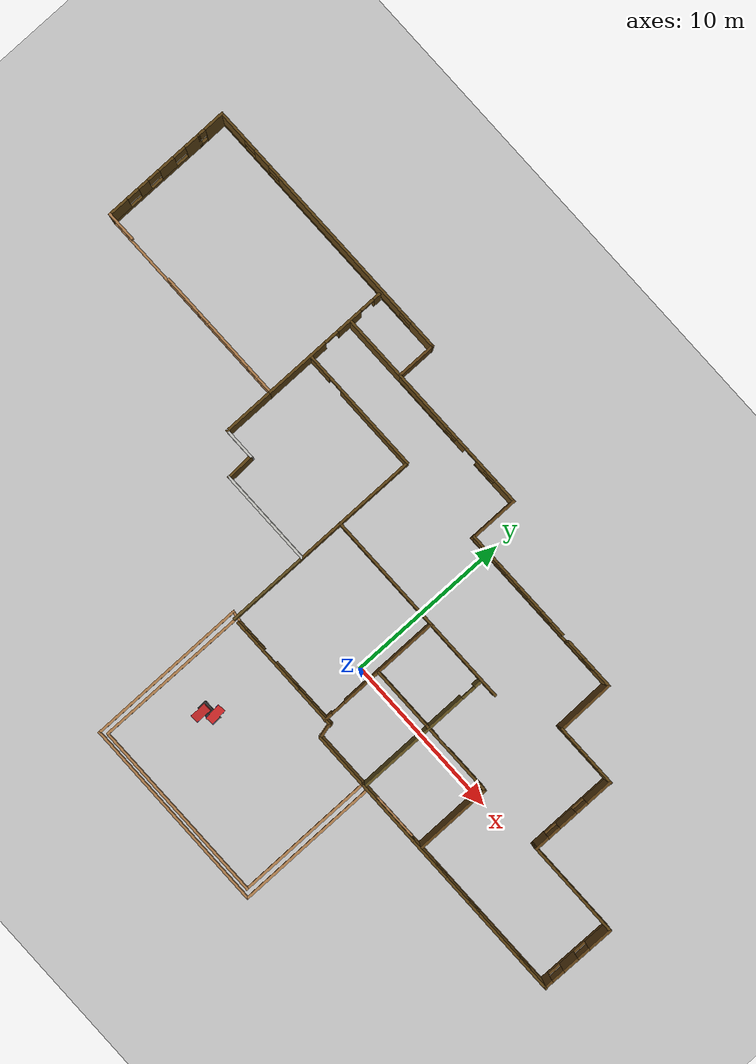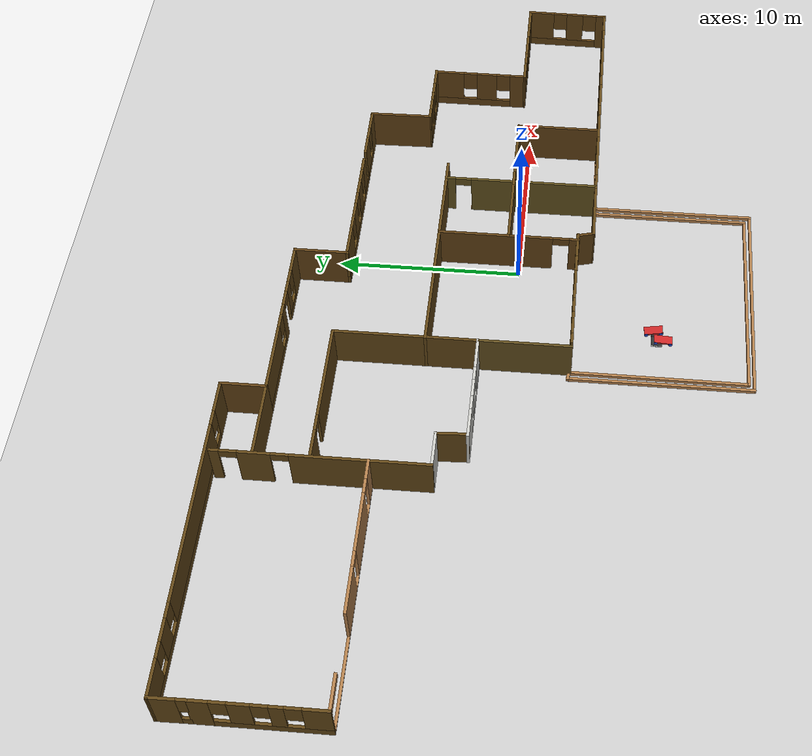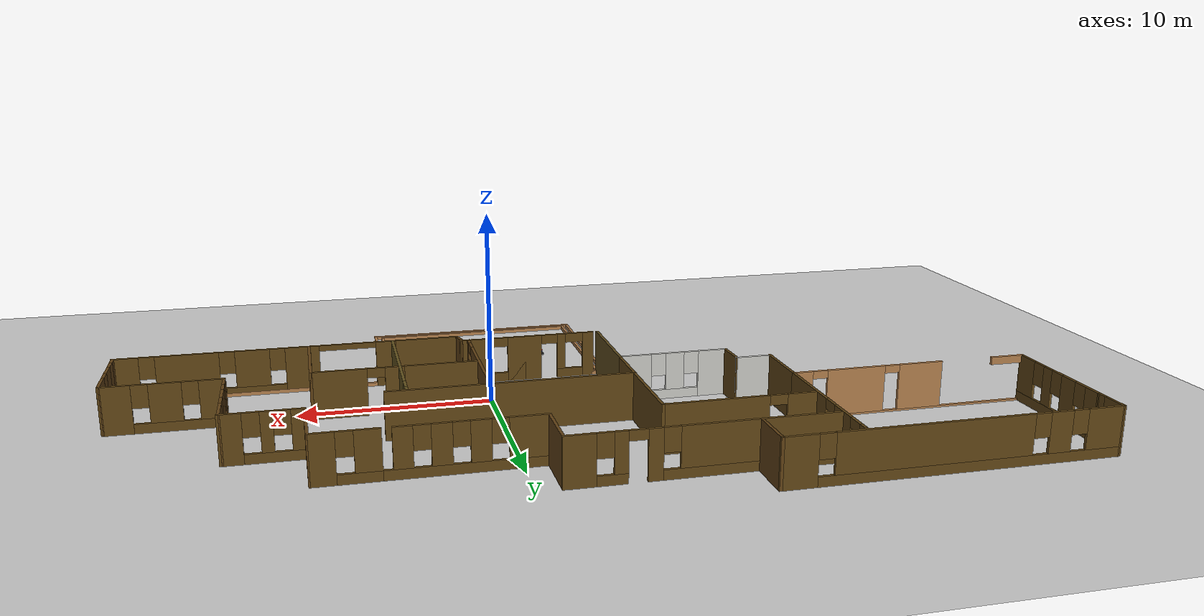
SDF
<sdf version="1.6">
 <world name="default">
  <plugin name="hellothere" filename="libhellothere.so"/>
  <light name="sun" type="directional">
   <pose>0 0 10 0 -0 0</pose>
   <diffuse>0.8 0.8 0.8 1</diffuse>
   <specular>0.2 0.2 0.2 1</specular>
   <attenuation>
    <range>1000</range>
    <constant>0.9</constant>
    <linear>0.01</linear>
    <quadratic>0.001</quadratic>
   </attenuation>
   <direction>-0.5 0.1 -0.9</direction>
  </light>
  <model name="ground_plane">
   <static>1</static>
   <link name="link">
    <collision name="collision">
     <geometry><plane><normal>0 0 1</normal><size>100 100</size></plane></geometry>
     <surface>
      <contact><collide_bitmask>65535</collide_bitmask></contact>
      <friction><ode><mu>100</mu><mu2>50</mu2></ode></friction>
     </surface>
    </collision>
    <visual name="visual">
     <cast_shadows>0</cast_shadows>
     <geometry><plane><normal>0 0 1</normal><size>100 100</size></plane></geometry>
     <material>
      <script><uri>file://media/materials/scripts/gazebo.material</uri><name>Gazebo/Grey</name></script>
     </material>
    </visual>
   </link>
  </model>
  <gravity>0 0 -9.8</gravity>
  <magnetic_field>6e-06 2.3e-05 -4.2e-05</magnetic_field>
  <atmosphere type="adiabatic"/>
  <physics name="default_physics" default="0" type="ode">
   <max_step_size>0.001</max_step_size>
   <real_time_factor>1</real_time_factor>
   <real_time_update_rate>1000</real_time_update_rate>
  </physics>
  <scene><ambient>0.4 0.4 0.4 1</ambient><background>0.7 0.7 0.7 1</background><shadows>1</shadows></scene>
  <spherical_coordinates>
   <surface_model>EARTH_WGS84</surface_model>
   <latitude_deg>0</latitude_deg>
   <longitude_deg>0</longitude_deg>
   <elevation>0</elevation>
   <heading_deg>0</heading_deg>
  </spherical_coordinates>
  <model name="BuildMyWorld">
   <pose>-3.99019 0.7838 0 0 -0 0</pose>
   <link name="Wall_100">
    <collision name="Wall_100_Collision">
     <geometry><box><size>12.25 0.15 0.2</size></box></geometry>
     <pose>0 0 0.1 0 -0 0</pose>
    </collision>
    <visual name="Wall_100_Visual">
     <pose>0 0 0.1 0 -0 0</pose>
     <geometry><box><size>12.25 0.15 0.2</size></box></geometry>
     <material>
      <script><uri>file://media/materials/scripts/gazebo.material</uri><name>Gazebo/Wood</name></script>
      <ambient>1 1 1 1</ambient>
     </material>
     <meta><layer>0</layer></meta>
    </visual>
    <pose>3.08619 -13.6873 0 0 0 -0.002893</pose>
   </link>
   <link name="Wall_101">
    <collision name="Wall_101_Collision">
     <geometry><box><size>8.965 0.15 0.2</size></box></geometry>
     <pose>0 0 0.1 0 -0 0</pose>
    </collision>
    <visual name="Wall_101_Visual">
     <pose>0 0 0.1 0 -0 0</pose>
     <geometry><box><size>8.965 0.15 0.2</size></box></geometry>
     <material>
      <script><uri>file://media/materials/scripts/gazebo.material</uri><name>Gazebo/Wood</name></script>
      <ambient>1 1 1 1</ambient>
     </material>
     <meta><layer>0</layer></meta>
    </visual>
    <pose>9.13619 -9.29728 0 0 -0 1.5708</pose>
   </link>
   <link name="Wall_104">
    <collision name="Wall_104_Collision">
     <geometry><box><size>5 0.15 2.5</size></box></geometry>
     <pose>0 0 1.25 0 -0 0</pose>
    </collision>
    <visual name="Wall_104_Visual">
     <pose>0 0 1.25 0 -0 0</pose>
     <geometry><box><size>5 0.15 2.5</size></box></geometry>
     <material>
      <script><uri>file://media/materials/scripts/gazebo.material</uri><name>Gazebo/Grey</name></script>
      <ambient>0.384314 0.305882 0.117647 1</ambient>
     </material>
     <meta><layer>0</layer></meta>
    </visual>
    <pose>-2.57572 -1.51375 0 0 0 -1.57084</pose>
   </link>
   <link name="Wall_106">
    <collision name="Wall_106_Collision">
     <geometry><box><size>9.59713 0.15 0.2</size></box></geometry>
     <pose>0 0 0.1 0 -0 0</pose>
    </collision>
    <visual name="Wall_106_Visual">
     <pose>0 0 0.1 0 -0 0</pose>
     <geometry><box><size>9.59713 0.15 0.2</size></box></geometry>
     <material>
      <script><uri>file://media/materials/scripts/gazebo.material</uri><name>Gazebo/Wood</name></script>
      <ambient>1 1 1 1</ambient>
     </material>
     <meta><layer>0</layer></meta>
    </visual>
    <pose>-2.59331 -8.66228 0 0 -0 1.56709</pose>
   </link>
   <link name="Wall_44">
    <pose>-23.1606 8.78629 0 0 0 -1.5708</pose>
    <visual name="Wall_44_Visual_0">
     <pose>-2.72951 0 1.25 0 -0 0</pose>
     <geometry><box><size>1.04099 0.15 2.5</size></box></geometry>
     <material>
      <script><uri>file://media/materials/scripts/gazebo.material</uri><name>Gazebo/Grey</name></script>
      <ambient>0.384314 0.27451 0.0862745 1</ambient>
     </material>
     <meta><layer>0</layer></meta>
    </visual>
    <collision name="Wall_44_Collision_0">
     <geometry><box><size>1.04099 0.15 2.5</size></box></geometry>
     <pose>-2.72951 0 1.25 0 -0 0</pose>
    </collision>
    <visual name="Wall_44_Visual_1">
     <pose>0.520493 0 0.25 0 -0 0</pose>
     <geometry><box><size>5.45901 0.15 0.5</size></box></geometry>
     <material>
      <script><uri>file://media/materials/scripts/gazebo.material</uri><name>Gazebo/Grey</name></script>
      <ambient>0.384314 0.27451 0.0862745 1</ambient>
     </material>
     <meta><layer>0</layer></meta>
    </visual>
    <collision name="Wall_44_Collision_1">
     <geometry><box><size>5.45901 0.15 0.5</size></box></geometry>
     <pose>0.520493 0 0.25 0 -0 0</pose>
    </collision>
    <visual name="Wall_44_Visual_2">
     <pose>-0.878007 0 1.5 0 -0 0</pose>
     <geometry><box><size>1.06201 0.15 2</size></box></geometry>
     <material>
      <script><uri>file://media/materials/scripts/gazebo.material</uri><name>Gazebo/Grey</name></script>
      <ambient>0.384314 0.27451 0.0862745 1</ambient>
     </material>
     <meta><layer>0</layer></meta>
    </visual>
    <collision name="Wall_44_Collision_2">
     <geometry><box><size>1.06201 0.15 2</size></box></geometry>
     <pose>-0.878007 0 1.5 0 -0 0</pose>
    </collision>
    <visual name="Wall_44_Visual_3">
     <pose>0.797805 0 1.5 0 -0 0</pose>
     <geometry><box><size>0.689611 0.15 2</size></box></geometry>
     <material>
      <script><uri>file://media/materials/scripts/gazebo.material</uri><name>Gazebo/Grey</name></script>
      <ambient>0.384314 0.27451 0.0862745 1</ambient>
     </material>
     <meta><layer>0</layer></meta>
    </visual>
    <collision name="Wall_44_Collision_3">
     <geometry><box><size>0.689611 0.15 2</size></box></geometry>
     <pose>0.797805 0 1.5 0 -0 0</pose>
    </collision>
    <visual name="Wall_44_Visual_4">
     <pose>2.59631 0 1.5 0 -0 0</pose>
     <geometry><box><size>1.30739 0.15 2</size></box></geometry>
     <material>
      <script><uri>file://media/materials/scripts/gazebo.material</uri><name>Gazebo/Grey</name></script>
      <ambient>0.384314 0.27451 0.0862745 1</ambient>
     </material>
     <meta><layer>0</layer></meta>
    </visual>
    <collision name="Wall_44_Collision_4">
     <geometry><box><size>1.30739 0.15 2</size></box></geometry>
     <pose>2.59631 0 1.5 0 -0 0</pose>
    </collision>
    <visual name="Wall_44_Visual_5">
     <pose>-1.80901 0 1.9 0 -0 0</pose>
     <geometry><box><size>0.8 0.15 1.2</size></box></geometry>
     <material>
      <script><uri>file://media/materials/scripts/gazebo.material</uri><name>Gazebo/Grey</name></script>
      <ambient>0.384314 0.27451 0.0862745 1</ambient>
     </material>
     <meta><layer>0</layer></meta>
    </visual>
    <collision name="Wall_44_Collision_5">
     <geometry><box><size>0.8 0.15 1.2</size></box></geometry>
     <pose>-1.80901 0 1.9 0 -0 0</pose>
    </collision>
    <visual name="Wall_44_Visual_6">
     <pose>0.052999 0 1.9 0 -0 0</pose>
     <geometry><box><size>0.8 0.15 1.2</size></box></geometry>
     <material>
      <script><uri>file://media/materials/scripts/gazebo.material</uri><name>Gazebo/Grey</name></script>
      <ambient>0.384314 0.27451 0.0862745 1</ambient>
     </material>
     <meta><layer>0</layer></meta>
    </visual>
    <collision name="Wall_44_Collision_6">
     <geometry><box><size>0.8 0.15 1.2</size></box></geometry>
     <pose>0.052999 0 1.9 0 -0 0</pose>
    </collision>
    <visual name="Wall_44_Visual_7">
     <pose>1.54261 0 1.9 0 -0 0</pose>
     <geometry><box><size>0.8 0.15 1.2</size></box></geometry>
     <material>
      <script><uri>file://media/materials/scripts/gazebo.material</uri><name>Gazebo/Grey</name></script>
      <ambient>0.384314 0.27451 0.0862745 1</ambient>
     </material>
     <meta><layer>0</layer></meta>
    </visual>
    <collision name="Wall_44_Collision_7">
     <geometry><box><size>0.8 0.15 1.2</size></box></geometry>
     <pose>1.54261 0 1.9 0 -0 0</pose>
    </collision>
   </link>
   <link name="Wall_45">
    <pose>-16.7356 5.61129 0 0 -0 0</pose>
    <visual name="Wall_45_Visual_0">
     <pose>-6.49366 0 1.25 0 -0 0</pose>
     <geometry><box><size>0.01268 0.15 2.5</size></box></geometry>
     <material>
      <script><uri>file://media/materials/scripts/gazebo.material</uri><name>Gazebo/Wood</name></script>
      <ambient>0.384314 0.27451 0.0862745 1</ambient>
     </material>
     <meta><layer>0</layer></meta>
    </visual>
    <collision name="Wall_45_Collision_0">
     <geometry><box><size>0.01268 0.15 2.5</size></box></geometry>
     <pose>-6.49366 0 1.25 0 -0 0</pose>
    </collision>
    <visual name="Wall_45_Visual_1">
     <pose>0.00634 0 0.05 0 -0 0</pose>
     <geometry><box><size>12.9873 0.15 0.1</size></box></geometry>
     <material>
      <script><uri>file://media/materials/scripts/gazebo.material</uri><name>Gazebo/Wood</name></script>
      <ambient>0.384314 0.27451 0.0862745 1</ambient>
     </material>
     <meta><layer>0</layer></meta>
    </visual>
    <collision name="Wall_45_Collision_1">
     <geometry><box><size>12.9873 0.15 0.1</size></box></geometry>
     <pose>0.00634 0 0.05 0 -0 0</pose>
    </collision>
    <visual name="Wall_45_Visual_2">
     <pose>-0.555122 0 1.3 0 -0 0</pose>
     <geometry><box><size>2.41817 0.15 2.4</size></box></geometry>
     <material>
      <script><uri>file://media/materials/scripts/gazebo.material</uri><name>Gazebo/Wood</name></script>
      <ambient>0.384314 0.27451 0.0862745 1</ambient>
     </material>
     <meta><layer>0</layer></meta>
    </visual>
    <collision name="Wall_45_Collision_2">
     <geometry><box><size>2.41817 0.15 2.4</size></box></geometry>
     <pose>-0.555122 0 1.3 0 -0 0</pose>
    </collision>
    <visual name="Wall_45_Visual_3">
     <pose>3.03034 0 1.3 0 -0 0</pose>
     <geometry><box><size>3.15275 0.15 2.4</size></box></geometry>
     <material>
      <script><uri>file://media/materials/scripts/gazebo.material</uri><name>Gazebo/Wood</name></script>
      <ambient>0.384314 0.27451 0.0862745 1</ambient>
     </material>
     <meta><layer>0</layer></meta>
    </visual>
    <collision name="Wall_45_Collision_3">
     <geometry><box><size>3.15275 0.15 2.4</size></box></geometry>
     <pose>3.03034 0 1.3 0 -0 0</pose>
    </collision>
    <visual name="Wall_45_Visual_4">
     <pose>5.95336 0 1.3 0 -0 0</pose>
     <geometry><box><size>1.09328 0.15 2.4</size></box></geometry>
     <material>
      <script><uri>file://media/materials/scripts/gazebo.material</uri><name>Gazebo/Wood</name></script>
      <ambient>0.384314 0.27451 0.0862745 1</ambient>
     </material>
     <meta><layer>0</layer></meta>
    </visual>
    <collision name="Wall_45_Collision_4">
     <geometry><box><size>1.09328 0.15 2.4</size></box></geometry>
     <pose>5.95336 0 1.3 0 -0 0</pose>
    </collision>
    <visual name="Wall_45_Visual_5">
     <pose>-5.55274 0 2.3 0 -0 0</pose>
     <geometry><box><size>1.86917 0.15 0.4</size></box></geometry>
     <material>
      <script><uri>file://media/materials/scripts/gazebo.material</uri><name>Gazebo/Wood</name></script>
      <ambient>0.384314 0.27451 0.0862745 1</ambient>
     </material>
     <meta><layer>0</layer></meta>
    </visual>
    <collision name="Wall_45_Collision_5">
     <geometry><box><size>1.86917 0.15 0.4</size></box></geometry>
     <pose>-5.55274 0 2.3 0 -0 0</pose>
    </collision>
    <visual name="Wall_45_Visual_6">
     <pose>1.05396 0 2.3 0 -0 0</pose>
     <geometry><box><size>0.8 0.15 0.4</size></box></geometry>
     <material>
      <script><uri>file://media/materials/scripts/gazebo.material</uri><name>Gazebo/Wood</name></script>
      <ambient>0.384314 0.27451 0.0862745 1</ambient>
     </material>
     <meta><layer>0</layer></meta>
    </visual>
    <collision name="Wall_45_Collision_6">
     <geometry><box><size>0.8 0.15 0.4</size></box></geometry>
     <pose>1.05396 0 2.3 0 -0 0</pose>
    </collision>
    <visual name="Wall_45_Visual_7">
     <pose>5.00672 0 2.3 0 -0 0</pose>
     <geometry><box><size>0.8 0.15 0.4</size></box></geometry>
     <material>
      <script><uri>file://media/materials/scripts/gazebo.material</uri><name>Gazebo/Wood</name></script>
      <ambient>0.384314 0.27451 0.0862745 1</ambient>
     </material>
     <meta><layer>0</layer></meta>
    </visual>
    <collision name="Wall_45_Collision_7">
     <geometry><box><size>0.8 0.15 0.4</size></box></geometry>
     <pose>5.00672 0 2.3 0 -0 0</pose>
    </collision>
   </link>
   <link name="Wall_46">
    <collision name="Wall_46_Collision">
     <geometry><box><size>3.25 0.15 2.5</size></box></geometry>
     <pose>0 0 1.25 0 -0 0</pose>
    </collision>
    <visual name="Wall_46_Visual">
     <pose>0 0 1.25 0 -0 0</pose>
     <geometry><box><size>3.25 0.15 2.5</size></box></geometry>
     <material>
      <script><uri>file://media/materials/scripts/gazebo.material</uri><name>Gazebo/Grey</name></script>
      <ambient>0.384314 0.27451 0.0862745 1</ambient>
     </material>
     <meta><layer>0</layer></meta>
    </visual>
    <pose>-10.3106 4.06129 0 0 0 -1.5708</pose>
   </link>
   <link name="Wall_47">
    <collision name="Wall_47_Collision">
     <geometry><box><size>2 0.15 2.5</size></box></geometry>
     <pose>0 0 1.25 0 -0 0</pose>
    </collision>
    <visual name="Wall_47_Visual">
     <pose>0 0 1.25 0 -0 0</pose>
     <geometry><box><size>2 0.15 2.5</size></box></geometry>
     <material>
      <script><uri>file://media/materials/scripts/gazebo.material</uri><name>Gazebo/CeilingTiled</name></script>
      <ambient>0.384314 0.27451 0.0862745 1</ambient>
     </material>
     <meta><layer>0</layer></meta>
    </visual>
    <pose>-9.3856 2.51129 0 0 -0 0</pose>
   </link>
   <link name="Wall_48">
    <collision name="Wall_48_Collision">
     <geometry><box><size>1.75153 0.15 2.5</size></box></geometry>
     <pose>0 0 1.25 0 -0 0</pose>
    </collision>
    <visual name="Wall_48_Visual">
     <pose>0 0 1.25 0 -0 0</pose>
     <geometry><box><size>1.75153 0.15 2.5</size></box></geometry>
     <material>
      <script><uri>file://media/materials/scripts/gazebo.material</uri><name>Gazebo/Grey</name></script>
      <ambient>0.384314 0.27451 0.0862745 1</ambient>
     </material>
     <meta><layer>0</layer></meta>
    </visual>
    <pose>-8.42562 1.71129 0 0 0 -1.5271</pose>
   </link>
   <link name="Wall_49">
    <pose>-5.50062 0.911286 0 0 -0 0</pose>
    <visual name="Wall_49_Visual_0">
     <pose>-2.18282 0 1.25 0 -0 0</pose>
     <geometry><box><size>1.63437 0.15 2.5</size></box></geometry>
     <material>
      <script><uri>file://media/materials/scripts/gazebo.material</uri><name>Gazebo/CeilingTiled</name></script>
      <ambient>0.384314 0.258824 0.0823529 1</ambient>
     </material>
     <meta><layer>0</layer></meta>
    </visual>
    <collision name="Wall_49_Collision_0">
     <geometry><box><size>1.63437 0.15 2.5</size></box></geometry>
     <pose>-2.18282 0 1.25 0 -0 0</pose>
    </collision>
    <visual name="Wall_49_Visual_1">
     <pose>0.817182 0 0.25 0 -0 0</pose>
     <geometry><box><size>4.36564 0.15 0.5</size></box></geometry>
     <material>
      <script><uri>file://media/materials/scripts/gazebo.material</uri><name>Gazebo/CeilingTiled</name></script>
      <ambient>0.384314 0.258824 0.0823529 1</ambient>
     </material>
     <meta><layer>0</layer></meta>
    </visual>
    <collision name="Wall_49_Collision_1">
     <geometry><box><size>4.36564 0.15 0.5</size></box></geometry>
     <pose>0.817182 0 0.25 0 -0 0</pose>
    </collision>
    <visual name="Wall_49_Visual_2">
     <pose>-0.068208 0 1.5 0 -0 0</pose>
     <geometry><box><size>0.994855 0.15 2</size></box></geometry>
     <material>
      <script><uri>file://media/materials/scripts/gazebo.material</uri><name>Gazebo/CeilingTiled</name></script>
      <ambient>0.384314 0.258824 0.0823529 1</ambient>
     </material>
     <meta><layer>0</layer></meta>
    </visual>
    <collision name="Wall_49_Collision_2">
     <geometry><box><size>0.994855 0.15 2</size></box></geometry>
     <pose>-0.068208 0 1.5 0 -0 0</pose>
    </collision>
    <visual name="Wall_49_Visual_3">
     <pose>2.11461 0 1.5 0 -0 0</pose>
     <geometry><box><size>1.77078 0.15 2</size></box></geometry>
     <material>
      <script><uri>file://media/materials/scripts/gazebo.material</uri><name>Gazebo/CeilingTiled</name></script>
      <ambient>0.384314 0.258824 0.0823529 1</ambient>
     </material>
     <meta><layer>0</layer></meta>
    </visual>
    <collision name="Wall_49_Collision_3">
     <geometry><box><size>1.77078 0.15 2</size></box></geometry>
     <pose>2.11461 0 1.5 0 -0 0</pose>
    </collision>
    <visual name="Wall_49_Visual_4">
     <pose>-0.965635 0 1.9 0 -0 0</pose>
     <geometry><box><size>0.8 0.15 1.2</size></box></geometry>
     <material>
      <script><uri>file://media/materials/scripts/gazebo.material</uri><name>Gazebo/CeilingTiled</name></script>
      <ambient>0.384314 0.258824 0.0823529 1</ambient>
     </material>
     <meta><layer>0</layer></meta>
    </visual>
    <collision name="Wall_49_Collision_4">
     <geometry><box><size>0.8 0.15 1.2</size></box></geometry>
     <pose>-0.965635 0 1.9 0 -0 0</pose>
    </collision>
    <visual name="Wall_49_Visual_5">
     <pose>0.82922 0 1.9 0 -0 0</pose>
     <geometry><box><size>0.8 0.15 1.2</size></box></geometry>
     <material>
      <script><uri>file://media/materials/scripts/gazebo.material</uri><name>Gazebo/CeilingTiled</name></script>
      <ambient>0.384314 0.258824 0.0823529 1</ambient>
     </material>
     <meta><layer>0</layer></meta>
    </visual>
    <collision name="Wall_49_Collision_5">
     <geometry><box><size>0.8 0.15 1.2</size></box></geometry>
     <pose>0.82922 0 1.9 0 -0 0</pose>
    </collision>
   </link>
   <link name="Wall_51">
    <collision name="Wall_51_Collision">
     <geometry><box><size>11.5 0.15 0.2</size></box></geometry>
     <pose>0 0 0.1 0 -0 0</pose>
    </collision>
    <visual name="Wall_51_Visual">
     <pose>0 0 0.1 0 -0 0</pose>
     <geometry><box><size>11.5 0.15 0.2</size></box></geometry>
     <material>
      <script><uri>file://media/materials/scripts/gazebo.material</uri><name>Gazebo/Wood</name></script>
      <ambient>1 1 1 1</ambient>
     </material>
     <meta><layer>0</layer></meta>
    </visual>
    <pose>3.06419 -13.3858 0 0 -0 0</pose>
   </link>
   <link name="Wall_52">
    <pose>8.73919 -4.86228 0 0 -0 1.5708</pose>
    <visual name="Wall_52_Visual_0">
     <pose>-0.730883 0 0.1 0 -0 0</pose>
     <geometry><box><size>15.7353 0.15 0.2</size></box></geometry>
     <material>
      <script><uri>file://media/materials/scripts/gazebo.material</uri><name>Gazebo/Wood</name></script>
      <ambient>1 1 1 1</ambient>
     </material>
     <meta><layer>0</layer></meta>
    </visual>
    <collision name="Wall_52_Collision_0">
     <geometry><box><size>15.7353 0.15 0.2</size></box></geometry>
     <pose>-0.730883 0 0.1 0 -0 0</pose>
    </collision>
    <visual name="Wall_52_Visual_1">
     <pose>8.31765 0 0.1 0 -0 0</pose>
     <geometry><box><size>0.561765 0.15 0.2</size></box></geometry>
     <material>
      <script><uri>file://media/materials/scripts/gazebo.material</uri><name>Gazebo/Wood</name></script>
      <ambient>1 1 1 1</ambient>
     </material>
     <meta><layer>0</layer></meta>
    </visual>
    <collision name="Wall_52_Collision_1">
     <geometry><box><size>0.561765 0.15 0.2</size></box></geometry>
     <pose>8.31765 0 0.1 0 -0 0</pose>
    </collision>
   </link>
   <link name="Wall_54">
    <pose>1.40983 -3.94563 0 0 -0 0</pose>
    <visual name="Wall_54_Visual_0">
     <pose>-3.4333 0 1.25 0 -0 0</pose>
     <geometry><box><size>0.63341 0.15 2.5</size></box></geometry>
     <material>
      <script><uri>file://media/materials/scripts/gazebo.material</uri><name>Gazebo/Grey</name></script>
      <ambient>0.384314 0.27451 0.0862745 1</ambient>
     </material>
     <meta><layer>0</layer></meta>
    </visual>
    <collision name="Wall_54_Collision_0">
     <geometry><box><size>0.63341 0.15 2.5</size></box></geometry>
     <pose>-3.4333 0 1.25 0 -0 0</pose>
    </collision>
    <visual name="Wall_54_Visual_1">
     <pose>0.17724 0 1.25 0 -0 0</pose>
     <geometry><box><size>1.89286 0.15 2.5</size></box></geometry>
     <material>
      <script><uri>file://media/materials/scripts/gazebo.material</uri><name>Gazebo/Grey</name></script>
      <ambient>0.384314 0.27451 0.0862745 1</ambient>
     </material>
     <meta><layer>0</layer></meta>
    </visual>
    <collision name="Wall_54_Collision_1">
     <geometry><box><size>1.89286 0.15 2.5</size></box></geometry>
     <pose>0.17724 0 1.25 0 -0 0</pose>
    </collision>
    <visual name="Wall_54_Visual_2">
     <pose>0.625547 0 1.25 0 -0 0</pose>
     <geometry><box><size>0.99625 0.15 2.5</size></box></geometry>
     <material>
      <script><uri>file://media/materials/scripts/gazebo.material</uri><name>Gazebo/Grey</name></script>
      <ambient>0.384314 0.27451 0.0862745 1</ambient>
     </material>
     <meta><layer>0</layer></meta>
    </visual>
    <collision name="Wall_54_Collision_2">
     <geometry><box><size>0.99625 0.15 2.5</size></box></geometry>
     <pose>0.625547 0 1.25 0 -0 0</pose>
    </collision>
    <visual name="Wall_54_Visual_3">
     <pose>-2.39289 0 0.25 0 -0 0</pose>
     <geometry><box><size>1.4474 0.15 0.5</size></box></geometry>
     <material>
      <script><uri>file://media/materials/scripts/gazebo.material</uri><name>Gazebo/Grey</name></script>
      <ambient>0.384314 0.27451 0.0862745 1</ambient>
     </material>
     <meta><layer>0</layer></meta>
    </visual>
    <collision name="Wall_54_Collision_3">
     <geometry><box><size>1.4474 0.15 0.5</size></box></geometry>
     <pose>-2.39289 0 0.25 0 -0 0</pose>
    </collision>
    <visual name="Wall_54_Visual_4">
     <pose>2.43684 0 0.25 0 -0 0</pose>
     <geometry><box><size>2.62633 0.15 0.5</size></box></geometry>
     <material>
      <script><uri>file://media/materials/scripts/gazebo.material</uri><name>Gazebo/Grey</name></script>
      <ambient>0.384314 0.27451 0.0862745 1</ambient>
     </material>
     <meta><layer>0</layer></meta>
    </visual>
    <collision name="Wall_54_Collision_4">
     <geometry><box><size>2.62633 0.15 0.5</size></box></geometry>
     <pose>2.43684 0 0.25 0 -0 0</pose>
    </collision>
    <visual name="Wall_54_Visual_5">
     <pose>2.43684 0 0.25 0 -0 0</pose>
     <geometry><box><size>2.62633 0.15 0.5</size></box></geometry>
     <material>
      <script><uri>file://media/materials/scripts/gazebo.material</uri><name>Gazebo/Grey</name></script>
      <ambient>0.384314 0.27451 0.0862745 1</ambient>
     </material>
     <meta><layer>0</layer></meta>
    </visual>
    <collision name="Wall_54_Collision_5">
     <geometry><box><size>2.62633 0.15 0.5</size></box></geometry>
     <pose>2.43684 0 0.25 0 -0 0</pose>
    </collision>
    <visual name="Wall_54_Visual_6">
     <pose>-1.89289 0 1.5 0 -0 0</pose>
     <geometry><box><size>0.447398 0.15 2</size></box></geometry>
     <material>
      <script><uri>file://media/materials/scripts/gazebo.material</uri><name>Gazebo/Grey</name></script>
      <ambient>0.384314 0.27451 0.0862745 1</ambient>
     </material>
     <meta><layer>0</layer></meta>
    </visual>
    <collision name="Wall_54_Collision_6">
     <geometry><box><size>0.447398 0.15 2</size></box></geometry>
     <pose>-1.89289 0 1.5 0 -0 0</pose>
    </collision>
    <visual name="Wall_54_Visual_7">
     <pose>-1.89289 0 1.5 0 -0 0</pose>
     <geometry><box><size>0.447398 0.15 2</size></box></geometry>
     <material>
      <script><uri>file://media/materials/scripts/gazebo.material</uri><name>Gazebo/Grey</name></script>
      <ambient>0.384314 0.27451 0.0862745 1</ambient>
     </material>
     <meta><layer>0</layer></meta>
    </visual>
    <collision name="Wall_54_Collision_7">
     <geometry><box><size>0.447398 0.15 2</size></box></geometry>
     <pose>-1.89289 0 1.5 0 -0 0</pose>
    </collision>
    <visual name="Wall_54_Visual_8">
     <pose>2.93684 0 1.5 0 -0 0</pose>
     <geometry><box><size>1.62633 0.15 2</size></box></geometry>
     <material>
      <script><uri>file://media/materials/scripts/gazebo.material</uri><name>Gazebo/Grey</name></script>
      <ambient>0.384314 0.27451 0.0862745 1</ambient>
     </material>
     <meta><layer>0</layer></meta>
    </visual>
    <collision name="Wall_54_Collision_8">
     <geometry><box><size>1.62633 0.15 2</size></box></geometry>
     <pose>2.93684 0 1.5 0 -0 0</pose>
    </collision>
    <visual name="Wall_54_Visual_9">
     <pose>2.93684 0 1.5 0 -0 0</pose>
     <geometry><box><size>1.62633 0.15 2</size></box></geometry>
     <material>
      <script><uri>file://media/materials/scripts/gazebo.material</uri><name>Gazebo/Grey</name></script>
      <ambient>0.384314 0.27451 0.0862745 1</ambient>
     </material>
     <meta><layer>0</layer></meta>
    </visual>
    <collision name="Wall_54_Collision_9">
     <geometry><box><size>1.62633 0.15 2</size></box></geometry>
     <pose>2.93684 0 1.5 0 -0 0</pose>
    </collision>
    <visual name="Wall_54_Visual_10">
     <pose>-2.61659 0 2.25 0 -0 0</pose>
     <geometry><box><size>1 0.15 0.5</size></box></geometry>
     <material>
      <script><uri>file://media/materials/scripts/gazebo.material</uri><name>Gazebo/Grey</name></script>
      <ambient>0.384314 0.27451 0.0862745 1</ambient>
     </material>
     <meta><layer>0</layer></meta>
    </visual>
    <collision name="Wall_54_Collision_10">
     <geometry><box><size>1 0.15 0.5</size></box></geometry>
     <pose>-2.61659 0 2.25 0 -0 0</pose>
    </collision>
    <visual name="Wall_54_Visual_11">
     <pose>1.62367 0 2.25 0 -0 0</pose>
     <geometry><box><size>1 0.15 0.5</size></box></geometry>
     <material>
      <script><uri>file://media/materials/scripts/gazebo.material</uri><name>Gazebo/Grey</name></script>
      <ambient>0.384314 0.27451 0.0862745 1</ambient>
     </material>
     <meta><layer>0</layer></meta>
    </visual>
    <collision name="Wall_54_Collision_11">
     <geometry><box><size>1 0.15 0.5</size></box></geometry>
     <pose>1.62367 0 2.25 0 -0 0</pose>
    </collision>
    <visual name="Wall_54_Visual_12">
     <pose>1.62367 0 2.25 0 -0 0</pose>
     <geometry><box><size>1 0.15 0.5</size></box></geometry>
     <material>
      <script><uri>file://media/materials/scripts/gazebo.material</uri><name>Gazebo/Grey</name></script>
      <ambient>0.384314 0.27451 0.0862745 1</ambient>
     </material>
     <meta><layer>0</layer></meta>
    </visual>
    <collision name="Wall_54_Collision_12">
     <geometry><box><size>1 0.15 0.5</size></box></geometry>
     <pose>1.62367 0 2.25 0 -0 0</pose>
    </collision>
    <visual name="Wall_54_Visual_13">
     <pose>-1.22088 0 2.25 0 -0 0</pose>
     <geometry><box><size>0.896613 0.15 0.5</size></box></geometry>
     <material>
      <script><uri>file://media/materials/scripts/gazebo.material</uri><name>Gazebo/Grey</name></script>
      <ambient>0.384314 0.27451 0.0862745 1</ambient>
     </material>
     <meta><layer>0</layer></meta>
    </visual>
    <collision name="Wall_54_Collision_13">
     <geometry><box><size>0.896613 0.15 0.5</size></box></geometry>
     <pose>-1.22088 0 2.25 0 -0 0</pose>
    </collision>
    <visual name="Wall_54_Visual_14">
     <pose>-1.22088 0 2.25 0 -0 0</pose>
     <geometry><box><size>0.896613 0.15 0.5</size></box></geometry>
     <material>
      <script><uri>file://media/materials/scripts/gazebo.material</uri><name>Gazebo/Grey</name></script>
      <ambient>0.384314 0.27451 0.0862745 1</ambient>
     </material>
     <meta><layer>0</layer></meta>
    </visual>
    <collision name="Wall_54_Collision_14">
     <geometry><box><size>0.896613 0.15 0.5</size></box></geometry>
     <pose>-1.22088 0 2.25 0 -0 0</pose>
    </collision>
   </link>
   <link name="Wall_55">
    <collision name="Wall_55_Collision">
     <geometry><box><size>1.02553 0.15 2.5</size></box></geometry>
     <pose>0 0 1.25 0 -0 0</pose>
    </collision>
    <visual name="Wall_55_Visual">
     <pose>0 0 1.25 0 -0 0</pose>
     <geometry><box><size>1.02553 0.15 2.5</size></box></geometry>
     <material>
      <script><uri>file://media/materials/scripts/gazebo.material</uri><name>Gazebo/Grey</name></script>
      <ambient>0.384314 0.258824 0.0823529 1</ambient>
     </material>
     <meta><layer>0</layer></meta>
    </visual>
    <pose>5.11981 -4.37063 0 0 0 -1.32872</pose>
   </link>
   <link name="Wall_56">
    <collision name="Wall_56_Collision">
     <geometry><box><size>3.43004 0.15 2.5</size></box></geometry>
     <pose>0 0 1.25 0 -0 0</pose>
    </collision>
    <visual name="Wall_56_Visual">
     <pose>0 0 1.25 0 -0 0</pose>
     <geometry><box><size>3.43004 0.15 2.5</size></box></geometry>
     <material>
      <script><uri>file://media/materials/scripts/gazebo.material</uri><name>Gazebo/Grey</name></script>
      <ambient>0.384314 0.27451 0.0862745 1</ambient>
     </material>
     <meta><layer>0</layer></meta>
    </visual>
    <pose>6.86477 -4.79563 0 0 -0 0</pose>
   </link>
   <link name="Wall_58">
    <pose>15.8398 -4.79563 0 0 -0 0</pose>
    <visual name="Wall_58_Visual_0">
     <pose>-6.78269 0 1.25 0 -0 0</pose>
     <geometry><box><size>1.18462 0.15 2.5</size></box></geometry>
     <material>
      <script><uri>file://media/materials/scripts/gazebo.material</uri><name>Gazebo/Grey</name></script>
      <ambient>0.384314 0.27451 0.0862745 1</ambient>
     </material>
     <meta><layer>0</layer></meta>
    </visual>
    <collision name="Wall_58_Collision_0">
     <geometry><box><size>1.18462 0.15 2.5</size></box></geometry>
     <pose>-6.78269 0 1.25 0 -0 0</pose>
    </collision>
    <visual name="Wall_58_Visual_1">
     <pose>0.592308 0 0.1 0 -0 0</pose>
     <geometry><box><size>13.5654 0.15 0.2</size></box></geometry>
     <material>
      <script><uri>file://media/materials/scripts/gazebo.material</uri><name>Gazebo/Wood</name></script>
      <ambient>0.384314 0.27451 0.0862745 1</ambient>
     </material>
     <meta><layer>0</layer></meta>
    </visual>
    <collision name="Wall_58_Collision_1">
     <geometry><box><size>13.5654 0.15 0.2</size></box></geometry>
     <pose>0.592308 0 0.1 0 -0 0</pose>
    </collision>
    <visual name="Wall_58_Visual_2">
     <pose>-2.29175 0 1.35 0 -0 0</pose>
     <geometry><box><size>1.79726 0.15 2.3</size></box></geometry>
     <material>
      <script><uri>file://media/materials/scripts/gazebo.material</uri><name>Gazebo/Grey</name></script>
      <ambient>0.384314 0.27451 0.0862745 1</ambient>
     </material>
     <meta><layer>0</layer></meta>
    </visual>
    <collision name="Wall_58_Collision_2">
     <geometry><box><size>1.79726 0.15 2.3</size></box></geometry>
     <pose>-2.29175 0 1.35 0 -0 0</pose>
    </collision>
    <visual name="Wall_58_Visual_3">
     <pose>2.99094 0 0.35 0 -0 0</pose>
     <geometry><box><size>8.76812 0.15 0.3</size></box></geometry>
     <material>
      <script><uri>file://media/materials/scripts/gazebo.material</uri><name>Gazebo/Grey</name></script>
      <ambient>0.384314 0.27451 0.0862745 1</ambient>
     </material>
     <meta><layer>0</layer></meta>
    </visual>
    <collision name="Wall_58_Collision_3">
     <geometry><box><size>8.76812 0.15 0.3</size></box></geometry>
     <pose>2.99094 0 0.35 0 -0 0</pose>
    </collision>
    <visual name="Wall_58_Visual_4">
     <pose>0.302195 0 1.5 0 -0 0</pose>
     <geometry><box><size>1.79063 0.15 2</size></box></geometry>
     <material>
      <script><uri>file://media/materials/scripts/gazebo.material</uri><name>Gazebo/Grey</name></script>
      <ambient>0.384314 0.27451 0.0862745 1</ambient>
     </material>
     <meta><layer>0</layer></meta>
    </visual>
    <collision name="Wall_58_Collision_4">
     <geometry><box><size>1.79063 0.15 2</size></box></geometry>
     <pose>0.302195 0 1.5 0 -0 0</pose>
    </collision>
    <visual name="Wall_58_Visual_5">
     <pose>3.60987 0 1.5 0 -0 0</pose>
     <geometry><box><size>3.22473 0.15 2</size></box></geometry>
     <material>
      <script><uri>file://media/materials/scripts/gazebo.material</uri><name>Gazebo/Grey</name></script>
      <ambient>0.384314 0.27451 0.0862745 1</ambient>
     </material>
     <meta><layer>0</layer></meta>
    </visual>
    <collision name="Wall_58_Collision_5">
     <geometry><box><size>3.22473 0.15 2</size></box></geometry>
     <pose>3.60987 0 1.5 0 -0 0</pose>
    </collision>
    <visual name="Wall_58_Visual_6">
     <pose>6.69862 0 1.5 0 -0 0</pose>
     <geometry><box><size>1.35277 0.15 2</size></box></geometry>
     <material>
      <script><uri>file://media/materials/scripts/gazebo.material</uri><name>Gazebo/Grey</name></script>
      <ambient>0.384314 0.27451 0.0862745 1</ambient>
     </material>
     <meta><layer>0</layer></meta>
    </visual>
    <collision name="Wall_58_Collision_6">
     <geometry><box><size>1.35277 0.15 2</size></box></geometry>
     <pose>6.69862 0 1.5 0 -0 0</pose>
    </collision>
    <visual name="Wall_58_Visual_7">
     <pose>-0.993119 0 1.9 0 -0 0</pose>
     <geometry><box><size>0.8 0.15 1.2</size></box></geometry>
     <material>
      <script><uri>file://media/materials/scripts/gazebo.material</uri><name>Gazebo/Grey</name></script>
      <ambient>0.384314 0.27451 0.0862745 1</ambient>
     </material>
     <meta><layer>0</layer></meta>
    </visual>
    <collision name="Wall_58_Collision_7">
     <geometry><box><size>0.8 0.15 1.2</size></box></geometry>
     <pose>-0.993119 0 1.9 0 -0 0</pose>
    </collision>
    <visual name="Wall_58_Visual_8">
     <pose>1.59751 0 1.9 0 -0 0</pose>
     <geometry><box><size>0.8 0.15 1.2</size></box></geometry>
     <material>
      <script><uri>file://media/materials/scripts/gazebo.material</uri><name>Gazebo/Grey</name></script>
      <ambient>0.384314 0.27451 0.0862745 1</ambient>
     </material>
     <meta><layer>0</layer></meta>
    </visual>
    <collision name="Wall_58_Collision_8">
     <geometry><box><size>0.8 0.15 1.2</size></box></geometry>
     <pose>1.59751 0 1.9 0 -0 0</pose>
    </collision>
    <visual name="Wall_58_Visual_9">
     <pose>5.62223 0 1.9 0 -0 0</pose>
     <geometry><box><size>0.8 0.15 1.2</size></box></geometry>
     <material>
      <script><uri>file://media/materials/scripts/gazebo.material</uri><name>Gazebo/Grey</name></script>
      <ambient>0.384314 0.27451 0.0862745 1</ambient>
     </material>
     <meta><layer>0</layer></meta>
    </visual>
    <collision name="Wall_58_Collision_9">
     <geometry><box><size>0.8 0.15 1.2</size></box></geometry>
     <pose>5.62223 0 1.9 0 -0 0</pose>
    </collision>
    <visual name="Wall_58_Visual_10">
     <pose>-4.69038 0 2.35 0 -0 0</pose>
     <geometry><box><size>3 0.15 0.3</size></box></geometry>
     <material>
      <script><uri>file://media/materials/scripts/gazebo.material</uri><name>Gazebo/Grey</name></script>
      <ambient>0.384314 0.27451 0.0862745 1</ambient>
     </material>
     <meta><layer>0</layer></meta>
    </visual>
    <collision name="Wall_58_Collision_10">
     <geometry><box><size>3 0.15 0.3</size></box></geometry>
     <pose>-4.69038 0 2.35 0 -0 0</pose>
    </collision>
   </link>
   <link name="Wall_59">
    <pose>23.1398 -2.49563 0 0 -0 1.55559</pose>
    <visual name="Wall_59_Visual_0">
     <pose>-2.07621 0 1.25 0 -0 0</pose>
     <geometry><box><size>0.597589 0.15 2.5</size></box></geometry>
     <material>
      <script><uri>file://media/materials/scripts/gazebo.material</uri><name>Gazebo/Grey</name></script>
      <ambient>0.384314 0.258824 0.0823529 1</ambient>
     </material>
     <meta><layer>0</layer></meta>
    </visual>
    <collision name="Wall_59_Collision_0">
     <geometry><box><size>0.597589 0.15 2.5</size></box></geometry>
     <pose>-2.07621 0 1.25 0 -0 0</pose>
    </collision>
    <visual name="Wall_59_Visual_1">
     <pose>0.298794 0 0.25 0 -0 0</pose>
     <geometry><box><size>4.15241 0.15 0.5</size></box></geometry>
     <material>
      <script><uri>file://media/materials/scripts/gazebo.material</uri><name>Gazebo/Grey</name></script>
      <ambient>0.384314 0.258824 0.0823529 1</ambient>
     </material>
     <meta><layer>0</layer></meta>
    </visual>
    <collision name="Wall_59_Collision_1">
     <geometry><box><size>4.15241 0.15 0.5</size></box></geometry>
     <pose>0.298794 0 0.25 0 -0 0</pose>
    </collision>
    <visual name="Wall_59_Visual_2">
     <pose>-0.474898 0 1.5 0 -0 0</pose>
     <geometry><box><size>1.00503 0.15 2</size></box></geometry>
     <material>
      <script><uri>file://media/materials/scripts/gazebo.material</uri><name>Gazebo/Grey</name></script>
      <ambient>0.384314 0.258824 0.0823529 1</ambient>
     </material>
     <meta><layer>0</layer></meta>
    </visual>
    <collision name="Wall_59_Collision_2">
     <geometry><box><size>1.00503 0.15 2</size></box></geometry>
     <pose>-0.474898 0 1.5 0 -0 0</pose>
    </collision>
    <visual name="Wall_59_Visual_3">
     <pose>1.60131 0 1.5 0 -0 0</pose>
     <geometry><box><size>1.54739 0.15 2</size></box></geometry>
     <material>
      <script><uri>file://media/materials/scripts/gazebo.material</uri><name>Gazebo/Grey</name></script>
      <ambient>0.384314 0.258824 0.0823529 1</ambient>
     </material>
     <meta><layer>0</layer></meta>
    </visual>
    <collision name="Wall_59_Collision_3">
     <geometry><box><size>1.54739 0.15 2</size></box></geometry>
     <pose>1.60131 0 1.5 0 -0 0</pose>
    </collision>
    <visual name="Wall_59_Visual_4">
     <pose>-1.37741 0 1.9 0 -0 0</pose>
     <geometry><box><size>0.8 0.15 1.2</size></box></geometry>
     <material>
      <script><uri>file://media/materials/scripts/gazebo.material</uri><name>Gazebo/Grey</name></script>
      <ambient>0.384314 0.258824 0.0823529 1</ambient>
     </material>
     <meta><layer>0</layer></meta>
    </visual>
    <collision name="Wall_59_Collision_4">
     <geometry><box><size>0.8 0.15 1.2</size></box></geometry>
     <pose>-1.37741 0 1.9 0 -0 0</pose>
    </collision>
    <visual name="Wall_59_Visual_5">
     <pose>0.427615 0 1.9 0 -0 0</pose>
     <geometry><box><size>0.8 0.15 1.2</size></box></geometry>
     <material>
      <script><uri>file://media/materials/scripts/gazebo.material</uri><name>Gazebo/Grey</name></script>
      <ambient>0.384314 0.258824 0.0823529 1</ambient>
     </material>
     <meta><layer>0</layer></meta>
    </visual>
    <collision name="Wall_59_Collision_5">
     <geometry><box><size>0.8 0.15 1.2</size></box></geometry>
     <pose>0.427615 0 1.9 0 -0 0</pose>
    </collision>
   </link>
   <link name="Wall_60">
    <pose>20.2498 -0.195633 0 0 -0 3.14159</pose>
    <visual name="Wall_60_Visual_0">
     <pose>-2.23109 0 1.25 0 -0 0</pose>
     <geometry><box><size>1.53781 0.15 2.5</size></box></geometry>
     <material>
      <script><uri>file://media/materials/scripts/gazebo.material</uri><name>Gazebo/Grey</name></script>
      <ambient>0.384314 0.27451 0.0862745 1</ambient>
     </material>
     <meta><layer>0</layer></meta>
    </visual>
    <collision name="Wall_60_Collision_0">
     <geometry><box><size>1.53781 0.15 2.5</size></box></geometry>
     <pose>-2.23109 0 1.25 0 -0 0</pose>
    </collision>
    <visual name="Wall_60_Visual_1">
     <pose>0.768905 0 0.25 0 -0 0</pose>
     <geometry><box><size>4.46219 0.15 0.5</size></box></geometry>
     <material>
      <script><uri>file://media/materials/scripts/gazebo.material</uri><name>Gazebo/Grey</name></script>
      <ambient>0.384314 0.27451 0.0862745 1</ambient>
     </material>
     <meta><layer>0</layer></meta>
    </visual>
    <collision name="Wall_60_Collision_1">
     <geometry><box><size>4.46219 0.15 0.5</size></box></geometry>
     <pose>0.768905 0 0.25 0 -0 0</pose>
    </collision>
    <visual name="Wall_60_Visual_2">
     <pose>0.117472 0 1.5 0 -0 0</pose>
     <geometry><box><size>1.55932 0.15 2</size></box></geometry>
     <material>
      <script><uri>file://media/materials/scripts/gazebo.material</uri><name>Gazebo/Grey</name></script>
      <ambient>0.384314 0.27451 0.0862745 1</ambient>
     </material>
     <meta><layer>0</layer></meta>
    </visual>
    <collision name="Wall_60_Collision_2">
     <geometry><box><size>1.55932 0.15 2</size></box></geometry>
     <pose>0.117472 0 1.5 0 -0 0</pose>
    </collision>
    <visual name="Wall_60_Visual_3">
     <pose>2.34857 0 1.5 0 -0 0</pose>
     <geometry><box><size>1.30287 0.15 2</size></box></geometry>
     <material>
      <script><uri>file://media/materials/scripts/gazebo.material</uri><name>Gazebo/Grey</name></script>
      <ambient>0.384314 0.27451 0.0862745 1</ambient>
     </material>
     <meta><layer>0</layer></meta>
    </visual>
    <collision name="Wall_60_Collision_3">
     <geometry><box><size>1.30287 0.15 2</size></box></geometry>
     <pose>2.34857 0 1.5 0 -0 0</pose>
    </collision>
    <visual name="Wall_60_Visual_4">
     <pose>-1.06219 0 1.9 0 -0 0</pose>
     <geometry><box><size>0.8 0.15 1.2</size></box></geometry>
     <material>
      <script><uri>file://media/materials/scripts/gazebo.material</uri><name>Gazebo/Grey</name></script>
      <ambient>0.384314 0.27451 0.0862745 1</ambient>
     </material>
     <meta><layer>0</layer></meta>
    </visual>
    <collision name="Wall_60_Collision_4">
     <geometry><box><size>0.8 0.15 1.2</size></box></geometry>
     <pose>-1.06219 0 1.9 0 -0 0</pose>
    </collision>
    <visual name="Wall_60_Visual_5">
     <pose>1.29713 0 1.9 0 -0 0</pose>
     <geometry><box><size>0.8 0.15 1.2</size></box></geometry>
     <material>
      <script><uri>file://media/materials/scripts/gazebo.material</uri><name>Gazebo/Grey</name></script>
      <ambient>0.384314 0.27451 0.0862745 1</ambient>
     </material>
     <meta><layer>0</layer></meta>
    </visual>
    <collision name="Wall_60_Collision_5">
     <geometry><box><size>0.8 0.15 1.2</size></box></geometry>
     <pose>1.29713 0 1.9 0 -0 0</pose>
    </collision>
   </link>
   <link name="Wall_61">
    <pose>17.334 2.45647 0 0 -0 1.56732</pose>
    <visual name="Wall_61_Visual_0">
     <pose>-2.25334 0 1.25 0 -0 0</pose>
     <geometry><box><size>0.94756 0.15 2.5</size></box></geometry>
     <material>
      <script><uri>file://media/materials/scripts/gazebo.material</uri><name>Gazebo/Grey</name></script>
      <ambient>0.384314 0.258824 0.0823529 1</ambient>
     </material>
     <meta><layer>0</layer></meta>
    </visual>
    <collision name="Wall_61_Collision_0">
     <geometry><box><size>0.94756 0.15 2.5</size></box></geometry>
     <pose>-2.25334 0 1.25 0 -0 0</pose>
    </collision>
    <visual name="Wall_61_Visual_1">
     <pose>0.47378 0 0.25 0 -0 0</pose>
     <geometry><box><size>4.50669 0.15 0.5</size></box></geometry>
     <material>
      <script><uri>file://media/materials/scripts/gazebo.material</uri><name>Gazebo/Grey</name></script>
      <ambient>0.384314 0.258824 0.0823529 1</ambient>
     </material>
     <meta><layer>0</layer></meta>
    </visual>
    <collision name="Wall_61_Collision_1">
     <geometry><box><size>4.50669 0.15 0.5</size></box></geometry>
     <pose>0.47378 0 0.25 0 -0 0</pose>
    </collision>
    <visual name="Wall_61_Visual_2">
     <pose>-0.385033 0 1.5 0 -0 0</pose>
     <geometry><box><size>1.18906 0.15 2</size></box></geometry>
     <material>
      <script><uri>file://media/materials/scripts/gazebo.material</uri><name>Gazebo/Grey</name></script>
      <ambient>0.384314 0.258824 0.0823529 1</ambient>
     </material>
     <meta><layer>0</layer></meta>
    </visual>
    <collision name="Wall_61_Collision_2">
     <geometry><box><size>1.18906 0.15 2</size></box></geometry>
     <pose>-0.385033 0 1.5 0 -0 0</pose>
    </collision>
    <visual name="Wall_61_Visual_3">
     <pose>1.86831 0 1.5 0 -0 0</pose>
     <geometry><box><size>1.71763 0.15 2</size></box></geometry>
     <material>
      <script><uri>file://media/materials/scripts/gazebo.material</uri><name>Gazebo/Grey</name></script>
      <ambient>0.384314 0.258824 0.0823529 1</ambient>
     </material>
     <meta><layer>0</layer></meta>
    </visual>
    <collision name="Wall_61_Collision_3">
     <geometry><box><size>1.71763 0.15 2</size></box></geometry>
     <pose>1.86831 0 1.5 0 -0 0</pose>
    </collision>
    <visual name="Wall_61_Visual_4">
     <pose>-1.37956 0 1.9 0 -0 0</pose>
     <geometry><box><size>0.8 0.15 1.2</size></box></geometry>
     <material>
      <script><uri>file://media/materials/scripts/gazebo.material</uri><name>Gazebo/Grey</name></script>
      <ambient>0.384314 0.258824 0.0823529 1</ambient>
     </material>
     <meta><layer>0</layer></meta>
    </visual>
    <collision name="Wall_61_Collision_4">
     <geometry><box><size>0.8 0.15 1.2</size></box></geometry>
     <pose>-1.37956 0 1.9 0 -0 0</pose>
    </collision>
    <visual name="Wall_61_Visual_5">
     <pose>0.609496 0 1.9 0 -0 0</pose>
     <geometry><box><size>0.8 0.15 1.2</size></box></geometry>
     <material>
      <script><uri>file://media/materials/scripts/gazebo.material</uri><name>Gazebo/Grey</name></script>
      <ambient>0.384314 0.258824 0.0823529 1</ambient>
     </material>
     <meta><layer>0</layer></meta>
    </visual>
    <collision name="Wall_61_Collision_5">
     <geometry><box><size>0.8 0.15 1.2</size></box></geometry>
     <pose>0.609496 0 1.9 0 -0 0</pose>
    </collision>
   </link>
   <link name="Wall_62">
    <pose>15.4532 5.10858 0 0 -0 3.14159</pose>
    <visual name="Wall_62_Visual_0">
     <pose>-1.44622 0 1.25 0 -0 0</pose>
     <geometry><box><size>1.10755 0.15 2.5</size></box></geometry>
     <material>
      <script><uri>file://media/materials/scripts/gazebo.material</uri><name>Gazebo/Grey</name></script>
      <ambient>0.384314 0.27451 0.0862745 1</ambient>
     </material>
     <meta><layer>0</layer></meta>
    </visual>
    <collision name="Wall_62_Collision_0">
     <geometry><box><size>1.10755 0.15 2.5</size></box></geometry>
     <pose>-1.44622 0 1.25 0 -0 0</pose>
    </collision>
    <visual name="Wall_62_Visual_1">
     <pose>0.553776 0 0.25 0 -0 0</pose>
     <geometry><box><size>2.89245 0.15 0.5</size></box></geometry>
     <material>
      <script><uri>file://media/materials/scripts/gazebo.material</uri><name>Gazebo/Grey</name></script>
      <ambient>0.384314 0.27451 0.0862745 1</ambient>
     </material>
     <meta><layer>0</layer></meta>
    </visual>
    <collision name="Wall_62_Collision_1">
     <geometry><box><size>2.89245 0.15 0.5</size></box></geometry>
     <pose>0.553776 0 0.25 0 -0 0</pose>
    </collision>
    <visual name="Wall_62_Visual_2">
     <pose>0.201469 0 1.5 0 -0 0</pose>
     <geometry><box><size>0.587836 0.15 2</size></box></geometry>
     <material>
      <script><uri>file://media/materials/scripts/gazebo.material</uri><name>Gazebo/Grey</name></script>
      <ambient>0.384314 0.27451 0.0862745 1</ambient>
     </material>
     <meta><layer>0</layer></meta>
    </visual>
    <collision name="Wall_62_Collision_2">
     <geometry><box><size>0.587836 0.15 2</size></box></geometry>
     <pose>0.201469 0 1.5 0 -0 0</pose>
    </collision>
    <visual name="Wall_62_Visual_3">
     <pose>1.64769 0 1.5 0 -0 0</pose>
     <geometry><box><size>0.704612 0.15 2</size></box></geometry>
     <material>
      <script><uri>file://media/materials/scripts/gazebo.material</uri><name>Gazebo/Grey</name></script>
      <ambient>0.384314 0.27451 0.0862745 1</ambient>
     </material>
     <meta><layer>0</layer></meta>
    </visual>
    <collision name="Wall_62_Collision_3">
     <geometry><box><size>0.704612 0.15 2</size></box></geometry>
     <pose>1.64769 0 1.5 0 -0 0</pose>
    </collision>
    <visual name="Wall_62_Visual_4">
     <pose>-0.492449 0 1.9 0 -0 0</pose>
     <geometry><box><size>0.8 0.15 1.2</size></box></geometry>
     <material>
      <script><uri>file://media/materials/scripts/gazebo.material</uri><name>Gazebo/Grey</name></script>
      <ambient>0.384314 0.27451 0.0862745 1</ambient>
     </material>
     <meta><layer>0</layer></meta>
    </visual>
    <collision name="Wall_62_Collision_4">
     <geometry><box><size>0.8 0.15 1.2</size></box></geometry>
     <pose>-0.492449 0 1.9 0 -0 0</pose>
    </collision>
    <visual name="Wall_62_Visual_5">
     <pose>0.895388 0 1.9 0 -0 0</pose>
     <geometry><box><size>0.8 0.15 1.2</size></box></geometry>
     <material>
      <script><uri>file://media/materials/scripts/gazebo.material</uri><name>Gazebo/Grey</name></script>
      <ambient>0.384314 0.27451 0.0862745 1</ambient>
     </material>
     <meta><layer>0</layer></meta>
    </visual>
    <collision name="Wall_62_Collision_5">
     <geometry><box><size>0.8 0.15 1.2</size></box></geometry>
     <pose>0.895388 0 1.9 0 -0 0</pose>
    </collision>
   </link>
   <link name="Wall_63">
    <collision name="Wall_63_Collision">
     <geometry><box><size>3.54621 0.15 2.5</size></box></geometry>
     <pose>0 0 1.25 0 -0 0</pose>
    </collision>
    <visual name="Wall_63_Visual">
     <pose>0 0 1.25 0 -0 0</pose>
     <geometry><box><size>3.54621 0.15 2.5</size></box></geometry>
     <material>
      <script><uri>file://media/materials/scripts/gazebo.material</uri><name>Gazebo/Grey</name></script>
      <ambient>0.384314 0.258824 0.0823529 1</ambient>
     </material>
     <meta><layer>0</layer></meta>
    </visual>
    <pose>13.5015 6.80647 0 0 -0 1.58653</pose>
   </link>
   <link name="Wall_64">
    <pose>11.9247 8.50437 0 0 -0 3.14159</pose>
    <visual name="Wall_64_Visual_0">
     <pose>-1.01058 0 1.25 0 -0 0</pose>
     <geometry><box><size>1.22884 0.15 2.5</size></box></geometry>
     <material>
      <script><uri>file://media/materials/scripts/gazebo.material</uri><name>Gazebo/Grey</name></script>
      <ambient>0.384314 0.27451 0.0862745 1</ambient>
     </material>
     <meta><layer>0</layer></meta>
    </visual>
    <collision name="Wall_64_Collision_0">
     <geometry><box><size>1.22884 0.15 2.5</size></box></geometry>
     <pose>-1.01058 0 1.25 0 -0 0</pose>
    </collision>
    <visual name="Wall_64_Visual_1">
     <pose>0.614419 0 0.25 0 -0 0</pose>
     <geometry><box><size>2.02116 0.15 0.5</size></box></geometry>
     <material>
      <script><uri>file://media/materials/scripts/gazebo.material</uri><name>Gazebo/Grey</name></script>
      <ambient>0.384314 0.27451 0.0862745 1</ambient>
     </material>
     <meta><layer>0</layer></meta>
    </visual>
    <collision name="Wall_64_Collision_1">
     <geometry><box><size>2.02116 0.15 0.5</size></box></geometry>
     <pose>0.614419 0 0.25 0 -0 0</pose>
    </collision>
    <visual name="Wall_64_Visual_2">
     <pose>1.01442 0 1.5 0 -0 0</pose>
     <geometry><box><size>1.22116 0.15 2</size></box></geometry>
     <material>
      <script><uri>file://media/materials/scripts/gazebo.material</uri><name>Gazebo/Grey</name></script>
      <ambient>0.384314 0.27451 0.0862745 1</ambient>
     </material>
     <meta><layer>0</layer></meta>
    </visual>
    <collision name="Wall_64_Collision_2">
     <geometry><box><size>1.22116 0.15 2</size></box></geometry>
     <pose>1.01442 0 1.5 0 -0 0</pose>
    </collision>
    <visual name="Wall_64_Visual_3">
     <pose>0.003837 0 1.9 0 -0 0</pose>
     <geometry><box><size>0.8 0.15 1.2</size></box></geometry>
     <material>
      <script><uri>file://media/materials/scripts/gazebo.material</uri><name>Gazebo/Grey</name></script>
      <ambient>0.384314 0.27451 0.0862745 1</ambient>
     </material>
     <meta><layer>0</layer></meta>
    </visual>
    <collision name="Wall_64_Collision_3">
     <geometry><box><size>0.8 0.15 1.2</size></box></geometry>
     <pose>0.003837 0 1.9 0 -0 0</pose>
    </collision>
   </link>
   <link name="Wall_65">
    <pose>6.57475 8.50437 0 0 -0 3.14159</pose>
    <visual name="Wall_65_Visual_0">
     <pose>0 0 0.25 0 -0 0</pose>
     <geometry><box><size>7.75 0.15 0.5</size></box></geometry>
     <material>
      <script><uri>file://media/materials/scripts/gazebo.material</uri><name>Gazebo/Grey</name></script>
      <ambient>0.384314 0.27451 0.0862745 1</ambient>
     </material>
     <meta><layer>0</layer></meta>
    </visual>
    <collision name="Wall_65_Collision_0">
     <geometry><box><size>7.75 0.15 0.5</size></box></geometry>
     <pose>0 0 0.25 0 -0 0</pose>
    </collision>
    <visual name="Wall_65_Visual_1">
     <pose>-2.82493 0 1.5 0 -0 0</pose>
     <geometry><box><size>0.911665 0.15 2</size></box></geometry>
     <material>
      <script><uri>file://media/materials/scripts/gazebo.material</uri><name>Gazebo/Grey</name></script>
      <ambient>0.384314 0.27451 0.0862745 1</ambient>
     </material>
     <meta><layer>0</layer></meta>
    </visual>
    <collision name="Wall_65_Collision_1">
     <geometry><box><size>0.911665 0.15 2</size></box></geometry>
     <pose>-2.82493 0 1.5 0 -0 0</pose>
    </collision>
    <visual name="Wall_65_Visual_2">
     <pose>-1.09013 0 1.5 0 -0 0</pose>
     <geometry><box><size>0.957926 0.15 2</size></box></geometry>
     <material>
      <script><uri>file://media/materials/scripts/gazebo.material</uri><name>Gazebo/Grey</name></script>
      <ambient>0.384314 0.27451 0.0862745 1</ambient>
     </material>
     <meta><layer>0</layer></meta>
    </visual>
    <collision name="Wall_65_Collision_2">
     <geometry><box><size>0.957926 0.15 2</size></box></geometry>
     <pose>-1.09013 0 1.5 0 -0 0</pose>
    </collision>
    <visual name="Wall_65_Visual_3">
     <pose>0.667795 0 1.5 0 -0 0</pose>
     <geometry><box><size>0.957926 0.15 2</size></box></geometry>
     <material>
      <script><uri>file://media/materials/scripts/gazebo.material</uri><name>Gazebo/Grey</name></script>
      <ambient>0.384314 0.27451 0.0862745 1</ambient>
     </material>
     <meta><layer>0</layer></meta>
    </visual>
    <collision name="Wall_65_Collision_3">
     <geometry><box><size>0.957926 0.15 2</size></box></geometry>
     <pose>0.667795 0 1.5 0 -0 0</pose>
    </collision>
    <visual name="Wall_65_Visual_4">
     <pose>2.91088 0 1.5 0 -0 0</pose>
     <geometry><box><size>1.92824 0.15 2</size></box></geometry>
     <material>
      <script><uri>file://media/materials/scripts/gazebo.material</uri><name>Gazebo/Grey</name></script>
      <ambient>0.384314 0.27451 0.0862745 1</ambient>
     </material>
     <meta><layer>0</layer></meta>
    </visual>
    <collision name="Wall_65_Collision_4">
     <geometry><box><size>1.92824 0.15 2</size></box></geometry>
     <pose>2.91088 0 1.5 0 -0 0</pose>
    </collision>
    <visual name="Wall_65_Visual_5">
     <pose>-1.96909 0 1.9 0 -0 0</pose>
     <geometry><box><size>0.8 0.15 1.2</size></box></geometry>
     <material>
      <script><uri>file://media/materials/scripts/gazebo.material</uri><name>Gazebo/Grey</name></script>
      <ambient>0.384314 0.27451 0.0862745 1</ambient>
     </material>
     <meta><layer>0</layer></meta>
    </visual>
    <collision name="Wall_65_Collision_5">
     <geometry><box><size>0.8 0.15 1.2</size></box></geometry>
     <pose>-1.96909 0 1.9 0 -0 0</pose>
    </collision>
    <visual name="Wall_65_Visual_6">
     <pose>-0.211168 0 1.9 0 -0 0</pose>
     <geometry><box><size>0.8 0.15 1.2</size></box></geometry>
     <material>
      <script><uri>file://media/materials/scripts/gazebo.material</uri><name>Gazebo/Grey</name></script>
      <ambient>0.384314 0.27451 0.0862745 1</ambient>
     </material>
     <meta><layer>0</layer></meta>
    </visual>
    <collision name="Wall_65_Collision_6">
     <geometry><box><size>0.8 0.15 1.2</size></box></geometry>
     <pose>-0.211168 0 1.9 0 -0 0</pose>
    </collision>
    <visual name="Wall_65_Visual_7">
     <pose>1.54676 0 1.9 0 -0 0</pose>
     <geometry><box><size>0.8 0.15 1.2</size></box></geometry>
     <material>
      <script><uri>file://media/materials/scripts/gazebo.material</uri><name>Gazebo/Grey</name></script>
      <ambient>0.384314 0.27451 0.0862745 1</ambient>
     </material>
     <meta><layer>0</layer></meta>
    </visual>
    <collision name="Wall_65_Collision_7">
     <geometry><box><size>0.8 0.15 1.2</size></box></geometry>
     <pose>1.54676 0 1.9 0 -0 0</pose>
    </collision>
   </link>
   <link name="Wall_66">
    <collision name="Wall_66_Collision">
     <geometry><box><size>3 0.15 2.5</size></box></geometry>
     <pose>0 0 1.25 0 -0 0</pose>
    </collision>
    <visual name="Wall_66_Visual">
     <pose>0 0 1.25 0 -0 0</pose>
     <geometry><box><size>3 0.15 2.5</size></box></geometry>
     <material>
      <script><uri>file://media/materials/scripts/gazebo.material</uri><name>Gazebo/Grey</name></script>
      <ambient>0.384314 0.258824 0.0823529 1</ambient>
     </material>
     <meta><layer>0</layer></meta>
    </visual>
    <pose>2.77475 9.92937 0 0 -0 1.5708</pose>
   </link>
   <link name="Wall_67">
    <pose>-1.77525 11.3544 0 0 -0 3.14159</pose>
    <visual name="Wall_67_Visual_0">
     <pose>-3.8555 0 1.25 0 -0 0</pose>
     <geometry><box><size>1.53901 0.15 2.5</size></box></geometry>
     <material>
      <script><uri>file://media/materials/scripts/gazebo.material</uri><name>Gazebo/Grey</name></script>
      <ambient>0.384314 0.27451 0.0862745 1</ambient>
     </material>
     <meta><layer>0</layer></meta>
    </visual>
    <collision name="Wall_67_Collision_0">
     <geometry><box><size>1.53901 0.15 2.5</size></box></geometry>
     <pose>-3.8555 0 1.25 0 -0 0</pose>
    </collision>
    <visual name="Wall_67_Visual_1">
     <pose>-0.385209 0 1.25 0 -0 0</pose>
     <geometry><box><size>0.704912 0.15 2.5</size></box></geometry>
     <material>
      <script><uri>file://media/materials/scripts/gazebo.material</uri><name>Gazebo/Grey</name></script>
      <ambient>0.384314 0.27451 0.0862745 1</ambient>
     </material>
     <meta><layer>0</layer></meta>
    </visual>
    <collision name="Wall_67_Collision_1">
     <geometry><box><size>0.704912 0.15 2.5</size></box></geometry>
     <pose>-0.385209 0 1.25 0 -0 0</pose>
    </collision>
    <visual name="Wall_67_Visual_2">
     <pose>-2.36183 0 0.25 0 -0 0</pose>
     <geometry><box><size>1.44833 0.15 0.5</size></box></geometry>
     <material>
      <script><uri>file://media/materials/scripts/gazebo.material</uri><name>Gazebo/Grey</name></script>
      <ambient>0.384314 0.27451 0.0862745 1</ambient>
     </material>
     <meta><layer>0</layer></meta>
    </visual>
    <collision name="Wall_67_Collision_2">
     <geometry><box><size>1.44833 0.15 0.5</size></box></geometry>
     <pose>-2.36183 0 0.25 0 -0 0</pose>
    </collision>
    <visual name="Wall_67_Visual_3">
     <pose>2.29612 0 0.25 0 -0 0</pose>
     <geometry><box><size>4.65775 0.15 0.5</size></box></geometry>
     <material>
      <script><uri>file://media/materials/scripts/gazebo.material</uri><name>Gazebo/Grey</name></script>
      <ambient>0.384314 0.27451 0.0862745 1</ambient>
     </material>
     <meta><layer>0</layer></meta>
    </visual>
    <collision name="Wall_67_Collision_3">
     <geometry><box><size>4.65775 0.15 0.5</size></box></geometry>
     <pose>2.29612 0 0.25 0 -0 0</pose>
    </collision>
    <visual name="Wall_67_Visual_4">
     <pose>-1.96183 0 1.5 0 -0 0</pose>
     <geometry><box><size>0.648328 0.15 2</size></box></geometry>
     <material>
      <script><uri>file://media/materials/scripts/gazebo.material</uri><name>Gazebo/Grey</name></script>
      <ambient>0.384314 0.27451 0.0862745 1</ambient>
     </material>
     <meta><layer>0</layer></meta>
    </visual>
    <collision name="Wall_67_Collision_4">
     <geometry><box><size>0.648328 0.15 2</size></box></geometry>
     <pose>-1.96183 0 1.5 0 -0 0</pose>
    </collision>
    <visual name="Wall_67_Visual_5">
     <pose>-1.96183 0 1.5 0 -0 0</pose>
     <geometry><box><size>0.648328 0.15 2</size></box></geometry>
     <material>
      <script><uri>file://media/materials/scripts/gazebo.material</uri><name>Gazebo/Grey</name></script>
      <ambient>0.384314 0.27451 0.0862745 1</ambient>
     </material>
     <meta><layer>0</layer></meta>
    </visual>
    <collision name="Wall_67_Collision_5">
     <geometry><box><size>0.648328 0.15 2</size></box></geometry>
     <pose>-1.96183 0 1.5 0 -0 0</pose>
    </collision>
    <visual name="Wall_67_Visual_6">
     <pose>2.69612 0 1.5 0 -0 0</pose>
     <geometry><box><size>3.85775 0.15 2</size></box></geometry>
     <material>
      <script><uri>file://media/materials/scripts/gazebo.material</uri><name>Gazebo/Grey</name></script>
      <ambient>0.384314 0.27451 0.0862745 1</ambient>
     </material>
     <meta><layer>0</layer></meta>
    </visual>
    <collision name="Wall_67_Collision_6">
     <geometry><box><size>3.85775 0.15 2</size></box></geometry>
     <pose>2.69612 0 1.5 0 -0 0</pose>
    </collision>
    <visual name="Wall_67_Visual_7">
     <pose>-2.68599 0 1.9 0 -0 0</pose>
     <geometry><box><size>0.8 0.15 1.2</size></box></geometry>
     <material>
      <script><uri>file://media/materials/scripts/gazebo.material</uri><name>Gazebo/Grey</name></script>
      <ambient>0.384314 0.27451 0.0862745 1</ambient>
     </material>
     <meta><layer>0</layer></meta>
    </visual>
    <collision name="Wall_67_Collision_7">
     <geometry><box><size>0.8 0.15 1.2</size></box></geometry>
     <pose>-2.68599 0 1.9 0 -0 0</pose>
    </collision>
    <visual name="Wall_67_Visual_8">
     <pose>0.367247 0 1.9 0 -0 0</pose>
     <geometry><box><size>0.8 0.15 1.2</size></box></geometry>
     <material>
      <script><uri>file://media/materials/scripts/gazebo.material</uri><name>Gazebo/Grey</name></script>
      <ambient>0.384314 0.27451 0.0862745 1</ambient>
     </material>
     <meta><layer>0</layer></meta>
    </visual>
    <collision name="Wall_67_Collision_8">
     <geometry><box><size>0.8 0.15 1.2</size></box></geometry>
     <pose>0.367247 0 1.9 0 -0 0</pose>
    </collision>
    <visual name="Wall_67_Visual_9">
     <pose>-1.18766 0 2.25 0 -0 0</pose>
     <geometry><box><size>0.9 0.15 0.5</size></box></geometry>
     <material>
      <script><uri>file://media/materials/scripts/gazebo.material</uri><name>Gazebo/Grey</name></script>
      <ambient>0.384314 0.27451 0.0862745 1</ambient>
     </material>
     <meta><layer>0</layer></meta>
    </visual>
    <collision name="Wall_67_Collision_9">
     <geometry><box><size>0.9 0.15 0.5</size></box></geometry>
     <pose>-1.18766 0 2.25 0 -0 0</pose>
    </collision>
    <visual name="Wall_67_Visual_10">
     <pose>-1.18766 0 2.25 0 -0 0</pose>
     <geometry><box><size>0.9 0.15 0.5</size></box></geometry>
     <material>
      <script><uri>file://media/materials/scripts/gazebo.material</uri><name>Gazebo/Grey</name></script>
      <ambient>0.384314 0.27451 0.0862745 1</ambient>
     </material>
     <meta><layer>0</layer></meta>
    </visual>
    <collision name="Wall_67_Collision_10">
     <geometry><box><size>0.9 0.15 0.5</size></box></geometry>
     <pose>-1.18766 0 2.25 0 -0 0</pose>
    </collision>
   </link>
   <link name="Wall_68">
    <collision name="Wall_68_Collision">
     <geometry><box><size>2.5 0.15 2.5</size></box></geometry>
     <pose>0 0 1.25 0 -0 0</pose>
    </collision>
    <visual name="Wall_68_Visual">
     <pose>0 0 1.25 0 -0 0</pose>
     <geometry><box><size>2.5 0.15 2.5</size></box></geometry>
     <material>
      <script><uri>file://media/materials/scripts/gazebo.material</uri><name>Gazebo/Grey</name></script>
      <ambient>0.384314 0.258824 0.0823529 1</ambient>
     </material>
     <meta><layer>0</layer></meta>
    </visual>
    <pose>-6.32525 12.5294 0 0 -0 1.5708</pose>
   </link>
   <link name="Wall_69">
    <pose>-14.7502 13.7044 0 0 -0 3.14159</pose>
    <visual name="Wall_69_Visual_0">
     <pose>-7.60811 0 1.25 0 -0 0</pose>
     <geometry><box><size>1.78377 0.15 2.5</size></box></geometry>
     <material>
      <script><uri>file://media/materials/scripts/gazebo.material</uri><name>Gazebo/Grey</name></script>
      <ambient>0.384314 0.27451 0.0862745 1</ambient>
     </material>
     <meta><layer>0</layer></meta>
    </visual>
    <collision name="Wall_69_Collision_0">
     <geometry><box><size>1.78377 0.15 2.5</size></box></geometry>
     <pose>-7.60811 0 1.25 0 -0 0</pose>
    </collision>
    <visual name="Wall_69_Visual_1">
     <pose>0.891886 0 0.25 0 -0 0</pose>
     <geometry><box><size>15.2162 0.15 0.5</size></box></geometry>
     <material>
      <script><uri>file://media/materials/scripts/gazebo.material</uri><name>Gazebo/Grey</name></script>
      <ambient>0.384314 0.27451 0.0862745 1</ambient>
     </material>
     <meta><layer>0</layer></meta>
    </visual>
    <collision name="Wall_69_Collision_1">
     <geometry><box><size>15.2162 0.15 0.5</size></box></geometry>
     <pose>0.891886 0 0.25 0 -0 0</pose>
    </collision>
    <visual name="Wall_69_Visual_2">
     <pose>-1.04245 0 1.5 0 -0 0</pose>
     <geometry><box><size>9.74756 0.15 2</size></box></geometry>
     <material>
      <script><uri>file://media/materials/scripts/gazebo.material</uri><name>Gazebo/Grey</name></script>
      <ambient>0.384314 0.27451 0.0862745 1</ambient>
     </material>
     <meta><layer>0</layer></meta>
    </visual>
    <collision name="Wall_69_Collision_2">
     <geometry><box><size>9.74756 0.15 2</size></box></geometry>
     <pose>-1.04245 0 1.5 0 -0 0</pose>
    </collision>
    <visual name="Wall_69_Visual_3">
     <pose>5.20282 0 1.5 0 -0 0</pose>
     <geometry><box><size>1.14297 0.15 2</size></box></geometry>
     <material>
      <script><uri>file://media/materials/scripts/gazebo.material</uri><name>Gazebo/Grey</name></script>
      <ambient>0.384314 0.27451 0.0862745 1</ambient>
     </material>
     <meta><layer>0</layer></meta>
    </visual>
    <collision name="Wall_69_Collision_3">
     <geometry><box><size>1.14297 0.15 2</size></box></geometry>
     <pose>5.20282 0 1.5 0 -0 0</pose>
    </collision>
    <visual name="Wall_69_Visual_4">
     <pose>7.53715 0 1.5 0 -0 0</pose>
     <geometry><box><size>1.9257 0.15 2</size></box></geometry>
     <material>
      <script><uri>file://media/materials/scripts/gazebo.material</uri><name>Gazebo/Grey</name></script>
      <ambient>0.384314 0.27451 0.0862745 1</ambient>
     </material>
     <meta><layer>0</layer></meta>
    </visual>
    <collision name="Wall_69_Collision_4">
     <geometry><box><size>1.9257 0.15 2</size></box></geometry>
     <pose>7.53715 0 1.5 0 -0 0</pose>
    </collision>
    <visual name="Wall_69_Visual_5">
     <pose>-6.31623 0 1.9 0 -0 0</pose>
     <geometry><box><size>0.8 0.15 1.2</size></box></geometry>
     <material>
      <script><uri>file://media/materials/scripts/gazebo.material</uri><name>Gazebo/Grey</name></script>
      <ambient>0.384314 0.27451 0.0862745 1</ambient>
     </material>
     <meta><layer>0</layer></meta>
    </visual>
    <collision name="Wall_69_Collision_5">
     <geometry><box><size>0.8 0.15 1.2</size></box></geometry>
     <pose>-6.31623 0 1.9 0 -0 0</pose>
    </collision>
    <visual name="Wall_69_Visual_6">
     <pose>4.23133 0 1.9 0 -0 0</pose>
     <geometry><box><size>0.8 0.15 1.2</size></box></geometry>
     <material>
      <script><uri>file://media/materials/scripts/gazebo.material</uri><name>Gazebo/Grey</name></script>
      <ambient>0.384314 0.27451 0.0862745 1</ambient>
     </material>
     <meta><layer>0</layer></meta>
    </visual>
    <collision name="Wall_69_Collision_6">
     <geometry><box><size>0.8 0.15 1.2</size></box></geometry>
     <pose>4.23133 0 1.9 0 -0 0</pose>
    </collision>
    <visual name="Wall_69_Visual_7">
     <pose>6.1743 0 1.9 0 -0 0</pose>
     <geometry><box><size>0.8 0.15 1.2</size></box></geometry>
     <material>
      <script><uri>file://media/materials/scripts/gazebo.material</uri><name>Gazebo/Grey</name></script>
      <ambient>0.384314 0.27451 0.0862745 1</ambient>
     </material>
     <meta><layer>0</layer></meta>
    </visual>
    <collision name="Wall_69_Collision_7">
     <geometry><box><size>0.8 0.15 1.2</size></box></geometry>
     <pose>6.1743 0 1.9 0 -0 0</pose>
    </collision>
   </link>
   <link name="Wall_70">
    <pose>-23.1679 12.8328 0 0 0 -1.56239</pose>
    <visual name="Wall_70_Visual_0">
     <pose>-0.272644 0 1.25 0 -0 0</pose>
     <geometry><box><size>1.34786 0.15 2.5</size></box></geometry>
     <material>
      <script><uri>file://media/materials/scripts/gazebo.material</uri><name>Gazebo/Grey</name></script>
      <ambient>0.384314 0.27451 0.0862745 1</ambient>
     </material>
     <meta><layer>0</layer></meta>
    </visual>
    <collision name="Wall_70_Collision_0">
     <geometry><box><size>1.34786 0.15 2.5</size></box></geometry>
     <pose>-0.272644 0 1.25 0 -0 0</pose>
    </collision>
    <visual name="Wall_70_Visual_1">
     <pose>0.673928 0 0.25 0 -0 0</pose>
     <geometry><box><size>0.545287 0.15 0.5</size></box></geometry>
     <material>
      <script><uri>file://media/materials/scripts/gazebo.material</uri><name>Gazebo/Grey</name></script>
      <ambient>0.384314 0.27451 0.0862745 1</ambient>
     </material>
     <meta><layer>0</layer></meta>
    </visual>
    <collision name="Wall_70_Collision_1">
     <geometry><box><size>0.545287 0.15 0.5</size></box></geometry>
     <pose>0.673928 0 0.25 0 -0 0</pose>
    </collision>
    <visual name="Wall_70_Visual_2">
     <pose>0.673928 0 1.9 0 -0 0</pose>
     <geometry><box><size>0.545287 0.15 1.2</size></box></geometry>
     <material>
      <script><uri>file://media/materials/scripts/gazebo.material</uri><name>Gazebo/Grey</name></script>
      <ambient>0.384314 0.27451 0.0862745 1</ambient>
     </material>
     <meta><layer>0</layer></meta>
    </visual>
    <collision name="Wall_70_Collision_2">
     <geometry><box><size>0.545287 0.15 1.2</size></box></geometry>
     <pose>0.673928 0 1.9 0 -0 0</pose>
    </collision>
   </link>
   <link name="Wall_72">
    <pose>-10.3106 9.53629 0 0 -0 1.5708</pose>
    <visual name="Wall_72_Visual_0">
     <pose>-1.98809 0 1.25 0 -0 0</pose>
     <geometry><box><size>4.02381 0.15 2.5</size></box></geometry>
     <material>
      <script><uri>file://media/materials/scripts/gazebo.material</uri><name>Gazebo/Grey</name></script>
      <ambient>0.384314 0.27451 0.0862745 1</ambient>
     </material>
     <meta><layer>0</layer></meta>
    </visual>
    <collision name="Wall_72_Collision_0">
     <geometry><box><size>4.02381 0.15 2.5</size></box></geometry>
     <pose>-1.98809 0 1.25 0 -0 0</pose>
    </collision>
    <visual name="Wall_72_Visual_1">
     <pose>1.75908 0 1.25 0 -0 0</pose>
     <geometry><box><size>1.67053 0.15 2.5</size></box></geometry>
     <material>
      <script><uri>file://media/materials/scripts/gazebo.material</uri><name>Gazebo/Grey</name></script>
      <ambient>0.384314 0.27451 0.0862745 1</ambient>
     </material>
     <meta><layer>0</layer></meta>
    </visual>
    <collision name="Wall_72_Collision_1">
     <geometry><box><size>1.67053 0.15 2.5</size></box></geometry>
     <pose>1.75908 0 1.25 0 -0 0</pose>
    </collision>
    <visual name="Wall_72_Visual_2">
     <pose>3.74717 0 1.25 0 -0 0</pose>
     <geometry><box><size>0.505657 0.15 2.5</size></box></geometry>
     <material>
      <script><uri>file://media/materials/scripts/gazebo.material</uri><name>Gazebo/Grey</name></script>
      <ambient>0.384314 0.27451 0.0862745 1</ambient>
     </material>
     <meta><layer>0</layer></meta>
    </visual>
    <collision name="Wall_72_Collision_2">
     <geometry><box><size>0.505657 0.15 2.5</size></box></geometry>
     <pose>3.74717 0 1.25 0 -0 0</pose>
    </collision>
    <visual name="Wall_72_Visual_3">
     <pose>0.47381 0 2.25 0 -0 0</pose>
     <geometry><box><size>0.9 0.15 0.5</size></box></geometry>
     <material>
      <script><uri>file://media/materials/scripts/gazebo.material</uri><name>Gazebo/Grey</name></script>
      <ambient>0.384314 0.27451 0.0862745 1</ambient>
     </material>
     <meta><layer>0</layer></meta>
    </visual>
    <collision name="Wall_72_Collision_3">
     <geometry><box><size>0.9 0.15 0.5</size></box></geometry>
     <pose>0.47381 0 2.25 0 -0 0</pose>
    </collision>
    <visual name="Wall_72_Visual_4">
     <pose>3.04434 0 2.25 0 -0 0</pose>
     <geometry><box><size>0.9 0.15 0.5</size></box></geometry>
     <material>
      <script><uri>file://media/materials/scripts/gazebo.material</uri><name>Gazebo/Grey</name></script>
      <ambient>0.384314 0.27451 0.0862745 1</ambient>
     </material>
     <meta><layer>0</layer></meta>
    </visual>
    <collision name="Wall_72_Collision_4">
     <geometry><box><size>0.9 0.15 0.5</size></box></geometry>
     <pose>3.04434 0 2.25 0 -0 0</pose>
    </collision>
   </link>
   <link name="Wall_74">
    <collision name="Wall_74_Collision">
     <geometry><box><size>4 0.15 2.5</size></box></geometry>
     <pose>0 0 1.25 0 -0 0</pose>
    </collision>
    <visual name="Wall_74_Visual">
     <pose>0 0 1.25 0 -0 0</pose>
     <geometry><box><size>4 0.15 2.5</size></box></geometry>
     <material>
      <script><uri>file://media/materials/scripts/gazebo.material</uri><name>Gazebo/Grey</name></script>
      <ambient>0.384314 0.27451 0.0862745 1</ambient>
     </material>
     <meta><layer>0</layer></meta>
    </visual>
    <pose>-8.25025 11.3544 0 0 -0 3.14159</pose>
   </link>
   <link name="Wall_81">
    <collision name="Wall_81_Collision">
     <geometry><box><size>7.74308 0.15 2.5</size></box></geometry>
     <pose>0 0 1.25 0 -0 0</pose>
    </collision>
    <visual name="Wall_81_Visual">
     <pose>0 0 1.25 0 -0 0</pose>
     <geometry><box><size>7.74308 0.15 2.5</size></box></geometry>
     <material>
      <script><uri>file://media/materials/scripts/gazebo.material</uri><name>Gazebo/Grey</name></script>
      <ambient>0.384314 0.27451 0.0862745 1</ambient>
     </material>
     <meta><layer>0</layer></meta>
    </visual>
    <pose>-2.57544 4.70783 0 0 0 -1.57085</pose>
   </link>
   <link name="Wall_83">
    <collision name="Wall_83_Collision">
     <geometry><box><size>12.5 0.15 2.5</size></box></geometry>
     <pose>0 0 1.25 0 -0 0</pose>
    </collision>
    <visual name="Wall_83_Visual">
     <pose>0 0 1.25 0 -0 0</pose>
     <geometry><box><size>12.5 0.15 2.5</size></box></geometry>
     <material>
      <script><uri>file://media/materials/scripts/gazebo.material</uri><name>Gazebo/Grey</name></script>
      <ambient>0.384314 0.27451 0.0862745 1</ambient>
     </material>
     <meta><layer>0</layer></meta>
    </visual>
    <pose>3.59865 3.66204 0 0 -0 0</pose>
   </link>
   <link name="Wall_85">
    <pose>4.6936 -0.171061 0 0 -0 1.5708</pose>
    <visual name="Wall_85_Visual_0">
     <pose>-3.58897 0 1.25 0 -0 0</pose>
     <geometry><box><size>0.57206 0.15 2.5</size></box></geometry>
     <material>
      <script><uri>file://media/materials/scripts/gazebo.material</uri><name>Gazebo/Grey</name></script>
      <ambient>0.384314 0.258824 0.0823529 1</ambient>
     </material>
     <meta><layer>0</layer></meta>
    </visual>
    <collision name="Wall_85_Collision_0">
     <geometry><box><size>0.57206 0.15 2.5</size></box></geometry>
     <pose>-3.58897 0 1.25 0 -0 0</pose>
    </collision>
    <visual name="Wall_85_Visual_1">
     <pose>0.73603 0 1.25 0 -0 0</pose>
     <geometry><box><size>6.27794 0.15 2.5</size></box></geometry>
     <material>
      <script><uri>file://media/materials/scripts/gazebo.material</uri><name>Gazebo/Grey</name></script>
      <ambient>0.384314 0.258824 0.0823529 1</ambient>
     </material>
     <meta><layer>0</layer></meta>
    </visual>
    <collision name="Wall_85_Collision_1">
     <geometry><box><size>6.27794 0.15 2.5</size></box></geometry>
     <pose>0.73603 0 1.25 0 -0 0</pose>
    </collision>
    <visual name="Wall_85_Visual_2">
     <pose>-2.85294 0 2.25 0 -0 0</pose>
     <geometry><box><size>0.9 0.15 0.5</size></box></geometry>
     <material>
      <script><uri>file://media/materials/scripts/gazebo.material</uri><name>Gazebo/Grey</name></script>
      <ambient>0.384314 0.258824 0.0823529 1</ambient>
     </material>
     <meta><layer>0</layer></meta>
    </visual>
    <collision name="Wall_85_Collision_2">
     <geometry><box><size>0.9 0.15 0.5</size></box></geometry>
     <pose>-2.85294 0 2.25 0 -0 0</pose>
    </collision>
   </link>
   <link name="Wall_88">
    <pose>-6.37525 8.50437 0 0 -0 3.14159</pose>
    <visual name="Wall_88_Visual_0">
     <pose>-1.1993 0 1.25 0 -0 0</pose>
     <geometry><box><size>5.35139 0.15 2.5</size></box></geometry>
     <material>
      <script><uri>file://media/materials/scripts/gazebo.material</uri><name>Gazebo/Grey</name></script>
      <ambient>0.384314 0.27451 0.0862745 1</ambient>
     </material>
     <meta><layer>0</layer></meta>
    </visual>
    <collision name="Wall_88_Collision_0">
     <geometry><box><size>5.35139 0.15 2.5</size></box></geometry>
     <pose>-1.1993 0 1.25 0 -0 0</pose>
    </collision>
    <visual name="Wall_88_Visual_1">
     <pose>3.1257 0 1.25 0 -0 0</pose>
     <geometry><box><size>1.49861 0.15 2.5</size></box></geometry>
     <material>
      <script><uri>file://media/materials/scripts/gazebo.material</uri><name>Gazebo/Grey</name></script>
      <ambient>0.384314 0.27451 0.0862745 1</ambient>
     </material>
     <meta><layer>0</layer></meta>
    </visual>
    <collision name="Wall_88_Collision_1">
     <geometry><box><size>1.49861 0.15 2.5</size></box></geometry>
     <pose>3.1257 0 1.25 0 -0 0</pose>
    </collision>
    <visual name="Wall_88_Visual_2">
     <pose>1.92639 0 2.25 0 -0 0</pose>
     <geometry><box><size>0.9 0.15 0.5</size></box></geometry>
     <material>
      <script><uri>file://media/materials/scripts/gazebo.material</uri><name>Gazebo/Grey</name></script>
      <ambient>0.384314 0.27451 0.0862745 1</ambient>
     </material>
     <meta><layer>0</layer></meta>
    </visual>
    <collision name="Wall_88_Collision_2">
     <geometry><box><size>0.9 0.15 0.5</size></box></geometry>
     <pose>1.92639 0 2.25 0 -0 0</pose>
    </collision>
   </link>
   <link name="Wall_90">
    <collision name="Wall_90_Collision">
     <geometry><box><size>4 0.15 2.5</size></box></geometry>
     <pose>0 0 1.25 0 -0 0</pose>
    </collision>
    <visual name="Wall_90_Visual">
     <pose>0 0 1.25 0 -0 0</pose>
     <geometry><box><size>4 0.15 2.5</size></box></geometry>
     <material>
      <script><uri>file://media/materials/scripts/gazebo.material</uri><name>Gazebo/Grey</name></script>
      <ambient>0.384314 0.27451 0.0862745 1</ambient>
     </material>
     <meta><layer>0</layer></meta>
    </visual>
    <pose>6.65746 -0.15118 0 0 -0 0</pose>
   </link>
   <link name="Wall_92">
    <pose>10.8825 -0.15118 0 0 -0 0</pose>
    <visual name="Wall_92_Visual_0">
     <pose>-1.88068 0 1.25 0 -0 0</pose>
     <geometry><box><size>0.988639 0.15 2.5</size></box></geometry>
     <material>
      <script><uri>file://media/materials/scripts/gazebo.material</uri><name>Gazebo/Grey</name></script>
      <ambient>0.384314 0.27451 0.0862745 1</ambient>
     </material>
     <meta><layer>0</layer></meta>
    </visual>
    <collision name="Wall_92_Collision_0">
     <geometry><box><size>0.988639 0.15 2.5</size></box></geometry>
     <pose>-1.88068 0 1.25 0 -0 0</pose>
    </collision>
    <visual name="Wall_92_Visual_1">
     <pose>0.94432 0 1.25 0 -0 0</pose>
     <geometry><box><size>2.86136 0.15 2.5</size></box></geometry>
     <material>
      <script><uri>file://media/materials/scripts/gazebo.material</uri><name>Gazebo/Grey</name></script>
      <ambient>0.384314 0.27451 0.0862745 1</ambient>
     </material>
     <meta><layer>0</layer></meta>
    </visual>
    <collision name="Wall_92_Collision_1">
     <geometry><box><size>2.86136 0.15 2.5</size></box></geometry>
     <pose>0.94432 0 1.25 0 -0 0</pose>
    </collision>
    <visual name="Wall_92_Visual_2">
     <pose>-0.936361 0 2.25 0 -0 0</pose>
     <geometry><box><size>0.9 0.15 0.5</size></box></geometry>
     <material>
      <script><uri>file://media/materials/scripts/gazebo.material</uri><name>Gazebo/Grey</name></script>
      <ambient>0.384314 0.27451 0.0862745 1</ambient>
     </material>
     <meta><layer>0</layer></meta>
    </visual>
    <collision name="Wall_92_Collision_2">
     <geometry><box><size>0.9 0.15 0.5</size></box></geometry>
     <pose>-0.936361 0 2.25 0 -0 0</pose>
    </collision>
   </link>
   <link name="Wall_93">
    <collision name="Wall_93_Collision">
     <geometry><box><size>4.75 0.15 2.5</size></box></geometry>
     <pose>0 0 1.25 0 -0 0</pose>
    </collision>
    <visual name="Wall_93_Visual">
     <pose>0 0 1.25 0 -0 0</pose>
     <geometry><box><size>4.75 0.15 2.5</size></box></geometry>
     <material>
      <script><uri>file://media/materials/scripts/gazebo.material</uri><name>Gazebo/Grey</name></script>
      <ambient>0.384314 0.258824 0.0823529 1</ambient>
     </material>
     <meta><layer>0</layer></meta>
    </visual>
    <pose>13.1825 -2.45118 0 0 0 -1.5708</pose>
   </link>
   <link name="Wall_98">
    <collision name="Wall_98_Collision">
     <geometry><box><size>0.854527 0.15 0.2</size></box></geometry>
     <pose>0 0 0.1 0 -0 0</pose>
    </collision>
    <visual name="Wall_98_Visual">
     <pose>0 0 0.1 0 -0 0</pose>
     <geometry><box><size>0.854527 0.15 0.2</size></box></geometry>
     <material>
      <script><uri>file://media/materials/scripts/gazebo.material</uri><name>Gazebo/Wood</name></script>
      <ambient>1 1 1 1</ambient>
     </material>
     <meta><layer>0</layer></meta>
    </visual>
    <pose>-2.61449 -3.90021 0 0 -0 3.01228</pose>
   </link>
   <link name="Wall_99">
    <collision name="Wall_99_Collision">
     <geometry><box><size>9.965 0.15 0.2</size></box></geometry>
     <pose>0 0 0.1 0 -0 0</pose>
    </collision>
    <visual name="Wall_99_Visual">
     <pose>0 0 0.1 0 -0 0</pose>
     <geometry><box><size>9.965 0.15 0.2</size></box></geometry>
     <material>
      <script><uri>file://media/materials/scripts/gazebo.material</uri><name>Gazebo/Wood</name></script>
      <ambient>1 1 1 1</ambient>
     </material>
     <meta><layer>0</layer></meta>
    </visual>
    <pose>-2.96381 -8.76228 0 0 0 -1.5708</pose>
   </link>
   <static>1</static>
  </model>
  <model name="AdditionalWall">
   <pose>4.74847 0.205813 0 0 -0 0</pose>
   <link name="Wall_115">
    <pose>0 0 0 0 0 -1.5708</pose>
    <visual name="Wall_115_Visual_0">
     <pose>-3.98651 0 1.25 0 -0 0</pose>
     <geometry><box><size>0.526987 0.15 2.5</size></box></geometry>
     <material>
      <script><uri>file://media/materials/scripts/gazebo.material</uri><name>Gazebo/Grey</name></script>
      <ambient>0.384314 0.317647 0.113725 1</ambient>
     </material>
     <meta><layer>0</layer></meta>
    </visual>
    <collision name="Wall_115_Collision_0">
     <geometry><box><size>0.526987 0.15 2.5</size></box></geometry>
     <pose>-3.98651 0 1.25 0 -0 0</pose>
    </collision>
    <visual name="Wall_115_Visual_1">
     <pose>0.713493 0 1.25 0 -0 0</pose>
     <geometry><box><size>7.07301 0.15 2.5</size></box></geometry>
     <material>
      <script><uri>file://media/materials/scripts/gazebo.material</uri><name>Gazebo/Grey</name></script>
      <ambient>0.384314 0.317647 0.113725 1</ambient>
     </material>
     <meta><layer>0</layer></meta>
    </visual>
    <collision name="Wall_115_Collision_1">
     <geometry><box><size>7.07301 0.15 2.5</size></box></geometry>
     <pose>0.713493 0 1.25 0 -0 0</pose>
    </collision>
    <visual name="Wall_115_Visual_2">
     <pose>-3.27301 0 2.25 0 -0 0</pose>
     <geometry><box><size>0.9 0.15 0.5</size></box></geometry>
     <material>
      <script><uri>file://media/materials/scripts/gazebo.material</uri><name>Gazebo/Grey</name></script>
      <ambient>0.384314 0.317647 0.113725 1</ambient>
     </material>
     <meta><layer>0</layer></meta>
    </visual>
    <collision name="Wall_115_Collision_2">
     <geometry><box><size>0.9 0.15 0.5</size></box></geometry>
     <pose>-3.27301 0 2.25 0 -0 0</pose>
    </collision>
   </link>
   <static>1</static>
  </model>
  <model name="4wheeler">
   <link name="link_0">
    <pose>0 0 0.04 0 -0 0</pose>
    <inertial>
     <mass>1</mass>
     <inertia>
      <ixx>0.166667</ixx>
      <ixy>0</ixy>
      <ixz>0</ixz>
      <iyy>0.166667</iyy>
      <iyz>0</iyz>
      <izz>0.166667</izz>
     </inertia>
    </inertial>
    <visual name="visual">
     <geometry><box><size>1 0.5 0.1</size></box></geometry>
     <material>
      <lighting>1</lighting>
      <script><uri>file://media/materials/scripts/gazebo.material</uri><name>Gazebo/RedBright</name></script>
      <shader type="vertex"><normal_map>__default__</normal_map></shader>
     </material>
    </visual>
    <collision name="collision">
     <geometry><box><size>1 0.5 0.1</size></box></geometry>
     <surface>
      <friction>
       <ode><mu>1</mu><mu2>1</mu2><fdir1>0 0 0</fdir1><slip1>0</slip1><slip2>0</slip2></ode>
       <torsional>
        <coefficient>1</coefficient>
        <patch_radius>0</patch_radius>
        <surface_radius>0</surface_radius>
        <use_patch_radius>1</use_patch_radius>
        <ode><slip>0</slip></ode>
       </torsional>
      </friction>
      <bounce><restitution_coefficient>0</restitution_coefficient><threshold>1e+06</threshold></bounce>
      <contact>
       <collide_without_contact>0</collide_without_contact>
       <collide_without_contact_bitmask>1</collide_without_contact_bitmask>
       <collide_bitmask>1</collide_bitmask>
       <ode>
        <soft_cfm>0</soft_cfm>
        <soft_erp>0.2</soft_erp>
        <kp>1e+13</kp>
        <kd>1</kd>
        <max_vel>0.01</max_vel>
        <min_depth>0</min_depth>
       </ode>
       <bullet>
        <split_impulse>1</split_impulse>
        <split_impulse_penetration_threshold>-0.01</split_impulse_penetration_threshold>
        <soft_cfm>0</soft_cfm>
        <soft_erp>0.2</soft_erp>
        <kp>1e+13</kp>
        <kd>1</kd>
       </bullet>
      </contact>
     </surface>
    </collision>
   </link>
   <link name="link_1">
    <pose>0.4 0.2575 -0.01 1.5708 -0 0</pose>
    <inertial>
     <mass>1</mass>
     <inertia><ixx>0.145833</ixx><ixy>0</ixy><ixz>0</ixz><iyy>0.145833</iyy><iyz>0</iyz><izz>0.125</izz></inertia>
    </inertial>
    <visual name="visual">
     <geometry><cylinder><radius>0.1</radius><length>0.015</length></cylinder></geometry>
     <material>
      <lighting>1</lighting>
      <script><uri>file://media/materials/scripts/gazebo.material</uri><name>Gazebo/Blue</name></script>
      <shader type="vertex"><normal_map>__default__</normal_map></shader>
     </material>
    </visual>
    <collision name="collision">
     <geometry><cylinder><radius>0.1</radius><length>0.015</length></cylinder></geometry>
     <surface>
      <friction>
       <ode><mu>1</mu><mu2>1</mu2><fdir1>0 0 0</fdir1><slip1>0</slip1><slip2>0</slip2></ode>
       <torsional>
        <coefficient>1</coefficient>
        <patch_radius>0</patch_radius>
        <surface_radius>0</surface_radius>
        <use_patch_radius>1</use_patch_radius>
        <ode><slip>0</slip></ode>
       </torsional>
      </friction>
      <bounce><restitution_coefficient>0</restitution_coefficient><threshold>1e+06</threshold></bounce>
      <contact>
       <collide_without_contact>0</collide_without_contact>
       <collide_without_contact_bitmask>1</collide_without_contact_bitmask>
       <collide_bitmask>1</collide_bitmask>
       <ode>
        <soft_cfm>0</soft_cfm>
        <soft_erp>0.2</soft_erp>
        <kp>1e+13</kp>
        <kd>1</kd>
        <max_vel>0.01</max_vel>
        <min_depth>0</min_depth>
       </ode>
       <bullet>
        <split_impulse>1</split_impulse>
        <split_impulse_penetration_threshold>-0.01</split_impulse_penetration_threshold>
        <soft_cfm>0</soft_cfm>
        <soft_erp>0.2</soft_erp>
        <kp>1e+13</kp>
        <kd>1</kd>
       </bullet>
      </contact>
     </surface>
    </collision>
   </link>
   <link name="link_1_clone">
    <pose>-0.4 0.2575 -0.01 1.5708 -0 0</pose>
    <inertial>
     <mass>1</mass>
     <inertia><ixx>0.145833</ixx><ixy>0</ixy><ixz>0</ixz><iyy>0.145833</iyy><iyz>0</iyz><izz>0.125</izz></inertia>
    </inertial>
    <visual name="visual">
     <geometry><cylinder><radius>0.1</radius><length>0.015</length></cylinder></geometry>
     <material>
      <lighting>1</lighting>
      <script><uri>file://media/materials/scripts/gazebo.material</uri><name>Gazebo/Blue</name></script>
      <shader type="vertex"><normal_map>__default__</normal_map></shader>
     </material>
    </visual>
    <collision name="collision">
     <geometry><cylinder><radius>0.1</radius><length>0.015</length></cylinder></geometry>
     <surface>
      <friction>
       <ode><mu>1</mu><mu2>1</mu2><fdir1>0 0 0</fdir1><slip1>0</slip1><slip2>0</slip2></ode>
       <torsional>
        <coefficient>1</coefficient>
        <patch_radius>0</patch_radius>
        <surface_radius>0</surface_radius>
        <use_patch_radius>1</use_patch_radius>
        <ode><slip>0</slip></ode>
       </torsional>
      </friction>
      <bounce><restitution_coefficient>0</restitution_coefficient><threshold>1e+06</threshold></bounce>
      <contact>
       <collide_without_contact>0</collide_without_contact>
       <collide_without_contact_bitmask>1</collide_without_contact_bitmask>
       <collide_bitmask>1</collide_bitmask>
       <ode>
        <soft_cfm>0</soft_cfm>
        <soft_erp>0.2</soft_erp>
        <kp>1e+13</kp>
        <kd>1</kd>
        <max_vel>0.01</max_vel>
        <min_depth>0</min_depth>
       </ode>
       <bullet>
        <split_impulse>1</split_impulse>
        <split_impulse_penetration_threshold>-0.01</split_impulse_penetration_threshold>
        <soft_cfm>0</soft_cfm>
        <soft_erp>0.2</soft_erp>
        <kp>1e+13</kp>
        <kd>1</kd>
       </bullet>
      </contact>
     </surface>
    </collision>
   </link>
   <link name="link_1_clone_0">
    <pose>0.4 -0.257501 -0.01 1.5708 -0 0</pose>
    <inertial>
     <mass>1</mass>
     <inertia><ixx>0.145833</ixx><ixy>0</ixy><ixz>0</ixz><iyy>0.145833</iyy><iyz>0</iyz><izz>0.125</izz></inertia>
    </inertial>
    <visual name="visual">
     <geometry><cylinder><radius>0.1</radius><length>0.015</length></cylinder></geometry>
     <material>
      <lighting>1</lighting>
      <script><uri>file://media/materials/scripts/gazebo.material</uri><name>Gazebo/Blue</name></script>
      <shader type="vertex"><normal_map>__default__</normal_map></shader>
     </material>
    </visual>
    <collision name="collision">
     <geometry><cylinder><radius>0.1</radius><length>0.015</length></cylinder></geometry>
     <surface>
      <friction>
       <ode><mu>1</mu><mu2>1</mu2><fdir1>0 0 0</fdir1><slip1>0</slip1><slip2>0</slip2></ode>
       <torsional>
        <coefficient>1</coefficient>
        <patch_radius>0</patch_radius>
        <surface_radius>0</surface_radius>
        <use_patch_radius>1</use_patch_radius>
        <ode><slip>0</slip></ode>
       </torsional>
      </friction>
      <bounce><restitution_coefficient>0</restitution_coefficient><threshold>1e+06</threshold></bounce>
      <contact>
       <collide_without_contact>0</collide_without_contact>
       <collide_without_contact_bitmask>1</collide_without_contact_bitmask>
       <collide_bitmask>1</collide_bitmask>
       <ode>
        <soft_cfm>0</soft_cfm>
        <soft_erp>0.2</soft_erp>
        <kp>1e+13</kp>
        <kd>1</kd>
        <max_vel>0.01</max_vel>
        <min_depth>0</min_depth>
       </ode>
       <bullet>
        <split_impulse>1</split_impulse>
        <split_impulse_penetration_threshold>-0.01</split_impulse_penetration_threshold>
        <soft_cfm>0</soft_cfm>
        <soft_erp>0.2</soft_erp>
        <kp>1e+13</kp>
        <kd>1</kd>
       </bullet>
      </contact>
     </surface>
    </collision>
   </link>
   <link name="link_1_clone_1">
    <pose>-0.4 -0.257501 -0.01 1.5708 -0 0</pose>
    <inertial>
     <mass>1</mass>
     <inertia><ixx>0.145833</ixx><ixy>0</ixy><ixz>0</ixz><iyy>0.145833</iyy><iyz>0</iyz><izz>0.125</izz></inertia>
    </inertial>
    <visual name="visual">
     <geometry><cylinder><radius>0.1</radius><length>0.015</length></cylinder></geometry>
     <material>
      <lighting>1</lighting>
      <script><uri>file://media/materials/scripts/gazebo.material</uri><name>Gazebo/Blue</name></script>
      <shader type="vertex"><normal_map>__default__</normal_map></shader>
     </material>
    </visual>
    <collision name="collision">
     <geometry><cylinder><radius>0.1</radius><length>0.015</length></cylinder></geometry>
     <surface>
      <friction>
       <ode><mu>1</mu><mu2>1</mu2><fdir1>0 0 0</fdir1><slip1>0</slip1><slip2>0</slip2></ode>
       <torsional>
        <coefficient>1</coefficient>
        <patch_radius>0</patch_radius>
        <surface_radius>0</surface_radius>
        <use_patch_radius>1</use_patch_radius>
        <ode><slip>0</slip></ode>
       </torsional>
      </friction>
      <bounce><restitution_coefficient>0</restitution_coefficient><threshold>1e+06</threshold></bounce>
      <contact>
       <collide_without_contact>0</collide_without_contact>
       <collide_without_contact_bitmask>1</collide_without_contact_bitmask>
       <collide_bitmask>1</collide_bitmask>
       <ode>
        <soft_cfm>0</soft_cfm>
        <soft_erp>0.2</soft_erp>
        <kp>1e+13</kp>
        <kd>1</kd>
        <max_vel>0.01</max_vel>
        <min_depth>0</min_depth>
       </ode>
       <bullet>
        <split_impulse>1</split_impulse>
        <split_impulse_penetration_threshold>-0.01</split_impulse_penetration_threshold>
        <soft_cfm>0</soft_cfm>
        <soft_erp>0.2</soft_erp>
        <kp>1e+13</kp>
        <kd>1</kd>
       </bullet>
      </contact>
     </surface>
    </collision>
   </link>
   <joint name="link_0_JOINT_0" type="revolute">
    <parent>link_0</parent>
    <child>link_1</child>
    <axis>
     <xyz>0 0 1</xyz>
     <use_parent_model_frame>0</use_parent_model_frame>
     <limit>
      <lower>-1.79769e+308</lower>
      <upper>1.79769e+308</upper>
      <effort>-1</effort>
      <velocity>-1</velocity>
     </limit>
     <dynamics>
      <spring_reference>0</spring_reference>
      <spring_stiffness>0</spring_stiffness>
      <damping>0</damping>
     </dynamics>
    </axis>
    <physics>
     <ode><limit><cfm>0</cfm><erp>0.2</erp></limit><suspension><cfm>0</cfm><erp>0.2</erp></suspension></ode>
    </physics>
   </joint>
   <joint name="link_0_JOINT_1" type="revolute">
    <parent>link_0</parent>
    <child>link_1_clone_1</child>
    <axis>
     <xyz>0 0 1</xyz>
     <use_parent_model_frame>0</use_parent_model_frame>
     <limit>
      <lower>-1.79769e+308</lower>
      <upper>1.79769e+308</upper>
      <effort>-1</effort>
      <velocity>-1</velocity>
     </limit>
     <dynamics>
      <spring_reference>0</spring_reference>
      <spring_stiffness>0</spring_stiffness>
      <damping>0</damping>
     </dynamics>
    </axis>
    <physics>
     <ode><limit><cfm>0</cfm><erp>0.2</erp></limit><suspension><cfm>0</cfm><erp>0.2</erp></suspension></ode>
    </physics>
   </joint>
   <joint name="link_0_JOINT_2" type="revolute">
    <parent>link_0</parent>
    <child>link_1_clone</child>
    <axis>
     <xyz>0 0 1</xyz>
     <use_parent_model_frame>0</use_parent_model_frame>
     <limit>
      <lower>-1.79769e+308</lower>
      <upper>1.79769e+308</upper>
      <effort>-1</effort>
      <velocity>-1</velocity>
     </limit>
     <dynamics>
      <spring_reference>0</spring_reference>
      <spring_stiffness>0</spring_stiffness>
      <damping>0</damping>
     </dynamics>
    </axis>
    <physics>
     <ode><limit><cfm>0</cfm><erp>0.2</erp></limit><suspension><cfm>0</cfm><erp>0.2</erp></suspension></ode>
    </physics>
   </joint>
   <joint name="link_0_JOINT_3" type="revolute">
    <parent>link_0</parent>
    <child>link_1_clone_0</child>
    <axis>
     <xyz>0 0 1</xyz>
     <use_parent_model_frame>0</use_parent_model_frame>
     <limit>
      <lower>-1.79769e+308</lower>
      <upper>1.79769e+308</upper>
      <effort>-1</effort>
      <velocity>-1</velocity>
     </limit>
     <dynamics>
      <spring_reference>0</spring_reference>
      <spring_stiffness>0</spring_stiffness>
      <damping>0</damping>
     </dynamics>
    </axis>
    <physics>
     <ode><limit><cfm>0</cfm><erp>0.2</erp></limit><suspension><cfm>0</cfm><erp>0.2</erp></suspension></ode>
    </physics>
   </joint>
   <static>0</static>
   <pose>-4.03739 -8.07348 0.15732 -0.003662 -0.097651 1.57839</pose>
  </model>
  <model name="4wheeler_0">
   <link name="link_0">
    <pose>0 0 0.04 0 -0 0</pose>
    <inertial>
     <mass>1</mass>
     <inertia>
      <ixx>0.166667</ixx>
      <ixy>0</ixy>
      <ixz>0</ixz>
      <iyy>0.166667</iyy>
      <iyz>0</iyz>
      <izz>0.166667</izz>
     </inertia>
    </inertial>
    <visual name="visual">
     <geometry><box><size>1 0.5 0.1</size></box></geometry>
     <material>
      <lighting>1</lighting>
      <script><uri>file://media/materials/scripts/gazebo.material</uri><name>Gazebo/RedBright</name></script>
      <shader type="vertex"><normal_map>__default__</normal_map></shader>
     </material>
    </visual>
    <collision name="collision">
     <geometry><box><size>1 0.5 0.1</size></box></geometry>
     <surface>
      <friction>
       <ode><mu>1</mu><mu2>1</mu2><fdir1>0 0 0</fdir1><slip1>0</slip1><slip2>0</slip2></ode>
       <torsional>
        <coefficient>1</coefficient>
        <patch_radius>0</patch_radius>
        <surface_radius>0</surface_radius>
        <use_patch_radius>1</use_patch_radius>
        <ode><slip>0</slip></ode>
       </torsional>
      </friction>
      <bounce><restitution_coefficient>0</restitution_coefficient><threshold>1e+06</threshold></bounce>
      <contact>
       <collide_without_contact>0</collide_without_contact>
       <collide_without_contact_bitmask>1</collide_without_contact_bitmask>
       <collide_bitmask>1</collide_bitmask>
       <ode>
        <soft_cfm>0</soft_cfm>
        <soft_erp>0.2</soft_erp>
        <kp>1e+13</kp>
        <kd>1</kd>
        <max_vel>0.01</max_vel>
        <min_depth>0</min_depth>
       </ode>
       <bullet>
        <split_impulse>1</split_impulse>
        <split_impulse_penetration_threshold>-0.01</split_impulse_penetration_threshold>
        <soft_cfm>0</soft_cfm>
        <soft_erp>0.2</soft_erp>
        <kp>1e+13</kp>
        <kd>1</kd>
       </bullet>
      </contact>
     </surface>
    </collision>
   </link>
   <link name="link_1">
    <pose>0.4 0.2575 -0.01 1.5708 -0 0</pose>
    <inertial>
     <mass>1</mass>
     <inertia><ixx>0.145833</ixx><ixy>0</ixy><ixz>0</ixz><iyy>0.145833</iyy><iyz>0</iyz><izz>0.125</izz></inertia>
    </inertial>
    <visual name="visual">
     <geometry><cylinder><radius>0.1</radius><length>0.015</length></cylinder></geometry>
     <material>
      <lighting>1</lighting>
      <script><uri>file://media/materials/scripts/gazebo.material</uri><name>Gazebo/Blue</name></script>
      <shader type="vertex"><normal_map>__default__</normal_map></shader>
     </material>
    </visual>
    <collision name="collision">
     <geometry><cylinder><radius>0.1</radius><length>0.015</length></cylinder></geometry>
     <surface>
      <friction>
       <ode><mu>1</mu><mu2>1</mu2><fdir1>0 0 0</fdir1><slip1>0</slip1><slip2>0</slip2></ode>
       <torsional>
        <coefficient>1</coefficient>
        <patch_radius>0</patch_radius>
        <surface_radius>0</surface_radius>
        <use_patch_radius>1</use_patch_radius>
        <ode><slip>0</slip></ode>
       </torsional>
      </friction>
      <bounce><restitution_coefficient>0</restitution_coefficient><threshold>1e+06</threshold></bounce>
      <contact>
       <collide_without_contact>0</collide_without_contact>
       <collide_without_contact_bitmask>1</collide_without_contact_bitmask>
       <collide_bitmask>1</collide_bitmask>
       <ode>
        <soft_cfm>0</soft_cfm>
        <soft_erp>0.2</soft_erp>
        <kp>1e+13</kp>
        <kd>1</kd>
        <max_vel>0.01</max_vel>
        <min_depth>0</min_depth>
       </ode>
       <bullet>
        <split_impulse>1</split_impulse>
        <split_impulse_penetration_threshold>-0.01</split_impulse_penetration_threshold>
        <soft_cfm>0</soft_cfm>
        <soft_erp>0.2</soft_erp>
        <kp>1e+13</kp>
        <kd>1</kd>
       </bullet>
      </contact>
     </surface>
    </collision>
   </link>
   <link name="link_1_clone">
    <pose>-0.4 0.2575 -0.01 1.5708 -0 0</pose>
    <inertial>
     <mass>1</mass>
     <inertia><ixx>0.145833</ixx><ixy>0</ixy><ixz>0</ixz><iyy>0.145833</iyy><iyz>0</iyz><izz>0.125</izz></inertia>
    </inertial>
    <visual name="visual">
     <geometry><cylinder><radius>0.1</radius><length>0.015</length></cylinder></geometry>
     <material>
      <lighting>1</lighting>
      <script><uri>file://media/materials/scripts/gazebo.material</uri><name>Gazebo/Blue</name></script>
      <shader type="vertex"><normal_map>__default__</normal_map></shader>
     </material>
    </visual>
    <collision name="collision">
     <geometry><cylinder><radius>0.1</radius><length>0.015</length></cylinder></geometry>
     <surface>
      <friction>
       <ode><mu>1</mu><mu2>1</mu2><fdir1>0 0 0</fdir1><slip1>0</slip1><slip2>0</slip2></ode>
       <torsional>
        <coefficient>1</coefficient>
        <patch_radius>0</patch_radius>
        <surface_radius>0</surface_radius>
        <use_patch_radius>1</use_patch_radius>
        <ode><slip>0</slip></ode>
       </torsional>
      </friction>
      <bounce><restitution_coefficient>0</restitution_coefficient><threshold>1e+06</threshold></bounce>
      <contact>
       <collide_without_contact>0</collide_without_contact>
       <collide_without_contact_bitmask>1</collide_without_contact_bitmask>
       <collide_bitmask>1</collide_bitmask>
       <ode>
        <soft_cfm>0</soft_cfm>
        <soft_erp>0.2</soft_erp>
        <kp>1e+13</kp>
        <kd>1</kd>
        <max_vel>0.01</max_vel>
        <min_depth>0</min_depth>
       </ode>
       <bullet>
        <split_impulse>1</split_impulse>
        <split_impulse_penetration_threshold>-0.01</split_impulse_penetration_threshold>
        <soft_cfm>0</soft_cfm>
        <soft_erp>0.2</soft_erp>
        <kp>1e+13</kp>
        <kd>1</kd>
       </bullet>
      </contact>
     </surface>
    </collision>
   </link>
   <link name="link_1_clone_0">
    <pose>0.4 -0.257501 -0.01 1.5708 -0 0</pose>
    <inertial>
     <mass>1</mass>
     <inertia><ixx>0.145833</ixx><ixy>0</ixy><ixz>0</ixz><iyy>0.145833</iyy><iyz>0</iyz><izz>0.125</izz></inertia>
    </inertial>
    <visual name="visual">
     <geometry><cylinder><radius>0.1</radius><length>0.015</length></cylinder></geometry>
     <material>
      <lighting>1</lighting>
      <script><uri>file://media/materials/scripts/gazebo.material</uri><name>Gazebo/Blue</name></script>
      <shader type="vertex"><normal_map>__default__</normal_map></shader>
     </material>
    </visual>
    <collision name="collision">
     <geometry><cylinder><radius>0.1</radius><length>0.015</length></cylinder></geometry>
     <surface>
      <friction>
       <ode><mu>1</mu><mu2>1</mu2><fdir1>0 0 0</fdir1><slip1>0</slip1><slip2>0</slip2></ode>
       <torsional>
        <coefficient>1</coefficient>
        <patch_radius>0</patch_radius>
        <surface_radius>0</surface_radius>
        <use_patch_radius>1</use_patch_radius>
        <ode><slip>0</slip></ode>
       </torsional>
      </friction>
      <bounce><restitution_coefficient>0</restitution_coefficient><threshold>1e+06</threshold></bounce>
      <contact>
       <collide_without_contact>0</collide_without_contact>
       <collide_without_contact_bitmask>1</collide_without_contact_bitmask>
       <collide_bitmask>1</collide_bitmask>
       <ode>
        <soft_cfm>0</soft_cfm>
        <soft_erp>0.2</soft_erp>
        <kp>1e+13</kp>
        <kd>1</kd>
        <max_vel>0.01</max_vel>
        <min_depth>0</min_depth>
       </ode>
       <bullet>
        <split_impulse>1</split_impulse>
        <split_impulse_penetration_threshold>-0.01</split_impulse_penetration_threshold>
        <soft_cfm>0</soft_cfm>
        <soft_erp>0.2</soft_erp>
        <kp>1e+13</kp>
        <kd>1</kd>
       </bullet>
      </contact>
     </surface>
    </collision>
   </link>
   <link name="link_1_clone_1">
    <pose>-0.4 -0.257501 -0.01 1.5708 -0 0</pose>
    <inertial>
     <mass>1</mass>
     <inertia><ixx>0.145833</ixx><ixy>0</ixy><ixz>0</ixz><iyy>0.145833</iyy><iyz>0</iyz><izz>0.125</izz></inertia>
    </inertial>
    <visual name="visual">
     <geometry><cylinder><radius>0.1</radius><length>0.015</length></cylinder></geometry>
     <material>
      <lighting>1</lighting>
      <script><uri>file://media/materials/scripts/gazebo.material</uri><name>Gazebo/Blue</name></script>
      <shader type="vertex"><normal_map>__default__</normal_map></shader>
     </material>
    </visual>
    <collision name="collision">
     <geometry><cylinder><radius>0.1</radius><length>0.015</length></cylinder></geometry>
     <surface>
      <friction>
       <ode><mu>1</mu><mu2>1</mu2><fdir1>0 0 0</fdir1><slip1>0</slip1><slip2>0</slip2></ode>
       <torsional>
        <coefficient>1</coefficient>
        <patch_radius>0</patch_radius>
        <surface_radius>0</surface_radius>
        <use_patch_radius>1</use_patch_radius>
        <ode><slip>0</slip></ode>
       </torsional>
      </friction>
      <bounce><restitution_coefficient>0</restitution_coefficient><threshold>1e+06</threshold></bounce>
      <contact>
       <collide_without_contact>0</collide_without_contact>
       <collide_without_contact_bitmask>1</collide_without_contact_bitmask>
       <collide_bitmask>1</collide_bitmask>
       <ode>
        <soft_cfm>0</soft_cfm>
        <soft_erp>0.2</soft_erp>
        <kp>1e+13</kp>
        <kd>1</kd>
        <max_vel>0.01</max_vel>
        <min_depth>0</min_depth>
       </ode>
       <bullet>
        <split_impulse>1</split_impulse>
        <split_impulse_penetration_threshold>-0.01</split_impulse_penetration_threshold>
        <soft_cfm>0</soft_cfm>
        <soft_erp>0.2</soft_erp>
        <kp>1e+13</kp>
        <kd>1</kd>
       </bullet>
      </contact>
     </surface>
    </collision>
   </link>
   <joint name="link_0_JOINT_0" type="revolute">
    <parent>link_0</parent>
    <child>link_1</child>
    <axis>
     <xyz>0 0 1</xyz>
     <use_parent_model_frame>0</use_parent_model_frame>
     <limit>
      <lower>-1.79769e+308</lower>
      <upper>1.79769e+308</upper>
      <effort>-1</effort>
      <velocity>-1</velocity>
     </limit>
     <dynamics>
      <spring_reference>0</spring_reference>
      <spring_stiffness>0</spring_stiffness>
      <damping>0</damping>
     </dynamics>
    </axis>
    <physics>
     <ode><limit><cfm>0</cfm><erp>0.2</erp></limit><suspension><cfm>0</cfm><erp>0.2</erp></suspension></ode>
    </physics>
   </joint>
   <joint name="link_0_JOINT_1" type="revolute">
    <parent>link_0</parent>
    <child>link_1_clone_1</child>
    <axis>
     <xyz>0 0 1</xyz>
     <use_parent_model_frame>0</use_parent_model_frame>
     <limit>
      <lower>-1.79769e+308</lower>
      <upper>1.79769e+308</upper>
      <effort>-1</effort>
      <velocity>-1</velocity>
     </limit>
     <dynamics>
      <spring_reference>0</spring_reference>
      <spring_stiffness>0</spring_stiffness>
      <damping>0</damping>
     </dynamics>
    </axis>
    <physics>
     <ode><limit><cfm>0</cfm><erp>0.2</erp></limit><suspension><cfm>0</cfm><erp>0.2</erp></suspension></ode>
    </physics>
   </joint>
   <joint name="link_0_JOINT_2" type="revolute">
    <parent>link_0</parent>
    <child>link_1_clone</child>
    <axis>
     <xyz>0 0 1</xyz>
     <use_parent_model_frame>0</use_parent_model_frame>
     <limit>
      <lower>-1.79769e+308</lower>
      <upper>1.79769e+308</upper>
      <effort>-1</effort>
      <velocity>-1</velocity>
     </limit>
     <dynamics>
      <spring_reference>0</spring_reference>
      <spring_stiffness>0</spring_stiffness>
      <damping>0</damping>
     </dynamics>
    </axis>
    <physics>
     <ode><limit><cfm>0</cfm><erp>0.2</erp></limit><suspension><cfm>0</cfm><erp>0.2</erp></suspension></ode>
    </physics>
   </joint>
   <joint name="link_0_JOINT_3" type="revolute">
    <parent>link_0</parent>
    <child>link_1_clone_0</child>
    <axis>
     <xyz>0 0 1</xyz>
     <use_parent_model_frame>0</use_parent_model_frame>
     <limit>
      <lower>-1.79769e+308</lower>
      <upper>1.79769e+308</upper>
      <effort>-1</effort>
      <velocity>-1</velocity>
     </limit>
     <dynamics>
      <spring_reference>0</spring_reference>
      <spring_stiffness>0</spring_stiffness>
      <damping>0</damping>
     </dynamics>
    </axis>
    <physics>
     <ode><limit><cfm>0</cfm><erp>0.2</erp></limit><suspension><cfm>0</cfm><erp>0.2</erp></suspension></ode>
    </physics>
   </joint>
   <static>0</static>
   <pose>-3.44628 -7.5395 0.164909 0.014326 0.104709 1.66417</pose>
  </model>
  <model name="frc2016_ramparts">
   <static>1</static>
   <link name="link">
    <visual name="platform">
     <pose>0 0 0.06967 0 -0 0</pose>
     <geometry><box><size>1.27 0.5969 0.003175</size></box></geometry>
    </visual>
    <collision name="platform">
     <pose>0 0 0.06967 0 -0 0</pose>
     <geometry><box><size>1.27 0.5969 0.003175</size></box></geometry>
    </collision>
    <visual name="ramp1">
     <pose>0.30472 0.00588 0.1109 -0.13 0 0</pose>
     <geometry><box><size>0.60957 0.588891 0.00462</size></box></geometry>
     <material><ambient>0.2 0.2 0.2 1</ambient><diffuse>0.2 0.2 0.2 1</diffuse></material>
    </visual>
    <collision name="ramp1">
     <pose>0.30472 0.00588 0.1109 -0.13 0 0</pose>
     <geometry><box><size>0.60957 0.588891 0.00462</size></box></geometry>
    </collision>
    <visual name="up1">
     <pose>0.30472 -0.28806 0.11072 0 -0 0</pose>
     <geometry><box><size>0.60957 0.00462 0.07872</size></box></geometry>
     <material><ambient>0.2 0.2 0.2 1</ambient><diffuse>0.2 0.2 0.2 1</diffuse></material>
    </visual>
    <collision name="up1">
     <pose>0.30472 -0.28806 0.11072 0 -0 0</pose>
     <geometry><box><size>0.60957 0.00462 0.07872</size></box></geometry>
    </collision>
    <visual name="ramp2">
     <pose>-0.30472 -0.00619 0.1109 0.13 -0 0</pose>
     <geometry><box><size>0.60957 0.588891 0.00462</size></box></geometry>
     <material><ambient>0.2 0.2 0.2 1</ambient><diffuse>0.2 0.2 0.2 1</diffuse></material>
    </visual>
    <collision name="ramp2">
     <pose>-0.30472 -0.00619 0.1109 0.13 -0 0</pose>
     <geometry><box><size>0.60957 0.588891 0.00462</size></box></geometry>
    </collision>
    <visual name="up2">
     <pose>-0.30472 0.28806 0.11072 0 -0 0</pose>
     <geometry><box><size>0.60957 0.00462 0.07872</size></box></geometry>
     <material><ambient>0.2 0.2 0.2 1</ambient><diffuse>0.2 0.2 0.2 1</diffuse></material>
    </visual>
    <collision name="up2">
     <pose>-0.30472 0.28806 0.11072 0 -0 0</pose>
     <geometry><box><size>0.60957 0.00462 0.07872</size></box></geometry>
    </collision>
   </link>
   <pose>-3.74841 -7.73292 -0.06049 0 -0 0</pose>
  </model>
 </world>
</sdf>
